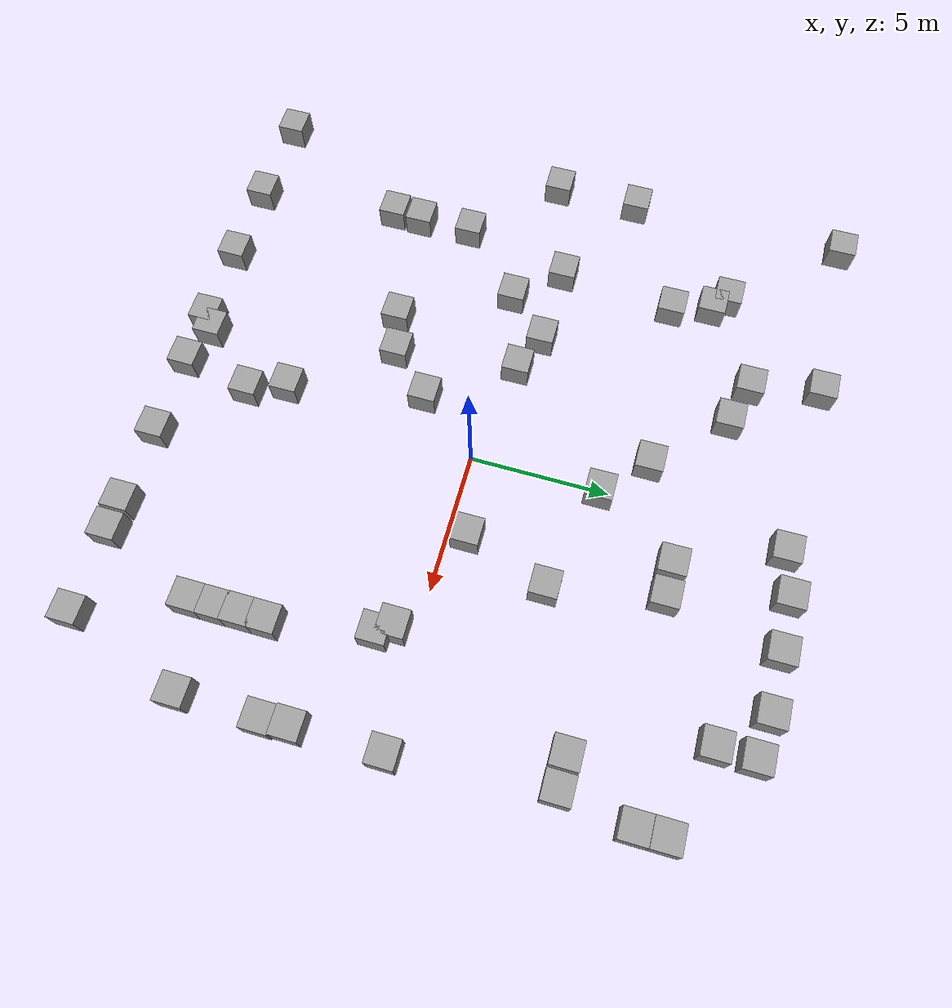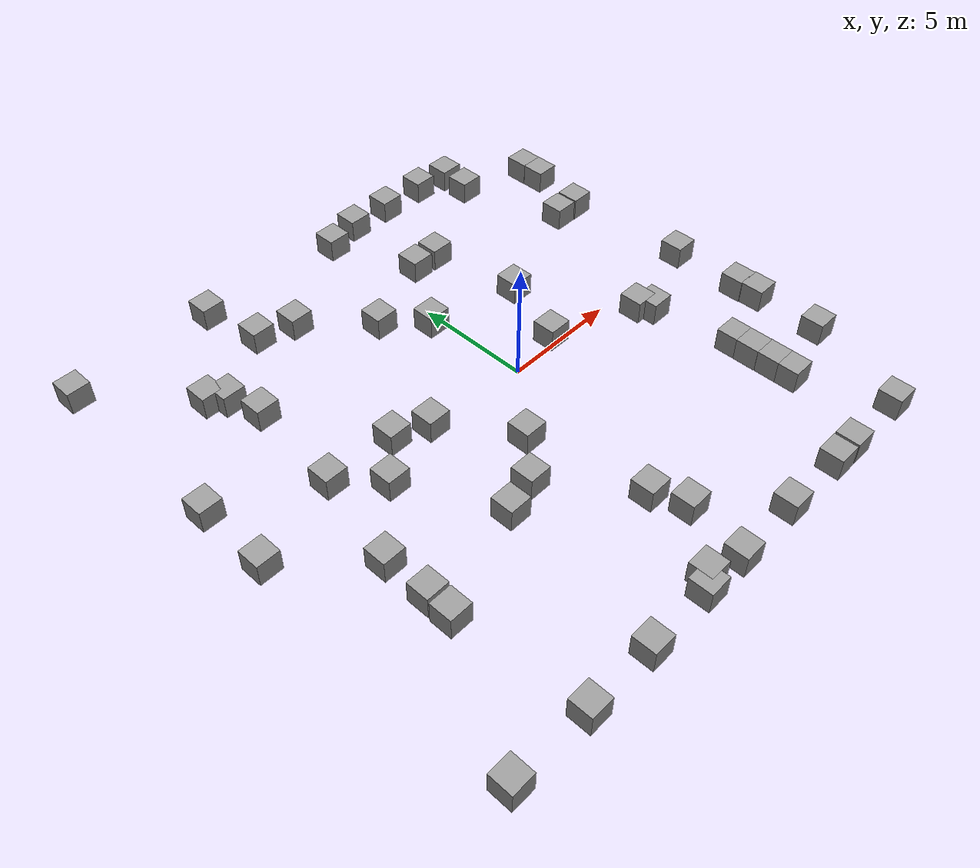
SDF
<?xml version='1.0'?>
<sdf version='1.7'>
  <model name='21'>
    <link name='link_0'>
      <inertial>
        <mass>1</mass>
        <inertia>
          <ixx>0.166667</ixx>
          <ixy>0</ixy>
          <ixz>0</ixz>
          <iyy>0.166667</iyy>
          <iyz>0</iyz>
          <izz>0.166667</izz>
        </inertia>
      </inertial>
      <pose>7.34424 10.0959 0 0 -0 0</pose>
      <visual name='visual'>
        <pose>0 0 0 0 -0 0</pose>
        <geometry>
          <box>
            <size>1 1 1</size>
          </box>
        </geometry>
        <material>
          <lighting>1</lighting>
          <script>
            <uri>file://media/materials/scripts/gazebo.material</uri>
            <name>Gazebo/Grey</name>
          </script>
          <shader type='pixel'/>
        </material>
        <transparency>0</transparency>
        <cast_shadows>1</cast_shadows>
      </visual>
      <collision name='collision'>
        <laser_retro>0</laser_retro>
        <max_contacts>10</max_contacts>
        <pose>0 0 0 0 -0 0</pose>
        <geometry>
          <box>
            <size>1 1 1</size>
          </box>
        </geometry>
        <surface>
          <friction>
            <ode>
              <mu>1</mu>
              <mu2>1</mu2>
              <fdir1>0 0 0</fdir1>
              <slip1>0</slip1>
              <slip2>0</slip2>
            </ode>
            <torsional>
              <coefficient>1</coefficient>
              <patch_radius>0</patch_radius>
              <surface_radius>0</surface_radius>
              <use_patch_radius>1</use_patch_radius>
              <ode>
                <slip>0</slip>
              </ode>
            </torsional>
          </friction>
          <bounce>
            <restitution_coefficient>0</restitution_coefficient>
            <threshold>1e+06</threshold>
          </bounce>
          <contact>
            <collide_without_contact>0</collide_without_contact>
            <collide_without_contact_bitmask>1</collide_without_contact_bitmask>
            <collide_bitmask>1</collide_bitmask>
            <ode>
              <soft_cfm>0</soft_cfm>
              <soft_erp>0.2</soft_erp>
              <kp>1e+13</kp>
              <kd>1</kd>
              <max_vel>0.01</max_vel>
              <min_depth>0</min_depth>
            </ode>
            <bullet>
              <split_impulse>1</split_impulse>
              <split_impulse_penetration_threshold>-0.01</split_impulse_penetration_threshold>
              <soft_cfm>0</soft_cfm>
              <soft_erp>0.2</soft_erp>
              <kp>1e+13</kp>
              <kd>1</kd>
            </bullet>
          </contact>
        </surface>
      </collision>
    </link>
    <link name='link_1'>
      <inertial>
        <mass>1</mass>
        <inertia>
          <ixx>0.166667</ixx>
          <ixy>0</ixy>
          <ixz>0</ixz>
          <iyy>0.166667</iyy>
          <iyz>0</iyz>
          <izz>0.166667</izz>
        </inertia>
      </inertial>
      <pose>10.3682 9.14937 0 0 -0 0</pose>
      <visual name='visual'>
        <pose>0 0 0 0 -0 0</pose>
        <geometry>
          <box>
            <size>1 1 1</size>
          </box>
        </geometry>
        <material>
          <lighting>1</lighting>
          <script>
            <uri>file://media/materials/scripts/gazebo.material</uri>
            <name>Gazebo/Grey</name>
          </script>
          <shader type='pixel'/>
        </material>
        <transparency>0</transparency>
        <cast_shadows>1</cast_shadows>
      </visual>
      <collision name='collision'>
        <laser_retro>0</laser_retro>
        <max_contacts>10</max_contacts>
        <pose>0 0 0 0 -0 0</pose>
        <geometry>
          <box>
            <size>1 1 1</size>
          </box>
        </geometry>
        <surface>
          <friction>
            <ode>
              <mu>1</mu>
              <mu2>1</mu2>
              <fdir1>0 0 0</fdir1>
              <slip1>0</slip1>
              <slip2>0</slip2>
            </ode>
            <torsional>
              <coefficient>1</coefficient>
              <patch_radius>0</patch_radius>
              <surface_radius>0</surface_radius>
              <use_patch_radius>1</use_patch_radius>
              <ode>
                <slip>0</slip>
              </ode>
            </torsional>
          </friction>
          <bounce>
            <restitution_coefficient>0</restitution_coefficient>
            <threshold>1e+06</threshold>
          </bounce>
          <contact>
            <collide_without_contact>0</collide_without_contact>
            <collide_without_contact_bitmask>1</collide_without_contact_bitmask>
            <collide_bitmask>1</collide_bitmask>
            <ode>
              <soft_cfm>0</soft_cfm>
              <soft_erp>0.2</soft_erp>
              <kp>1e+13</kp>
              <kd>1</kd>
              <max_vel>0.01</max_vel>
              <min_depth>0</min_depth>
            </ode>
            <bullet>
              <split_impulse>1</split_impulse>
              <split_impulse_penetration_threshold>-0.01</split_impulse_penetration_threshold>
              <soft_cfm>0</soft_cfm>
              <soft_erp>0.2</soft_erp>
              <kp>1e+13</kp>
              <kd>1</kd>
            </bullet>
          </contact>
        </surface>
      </collision>
    </link>
    <link name='link_10'>
      <inertial>
        <mass>1</mass>
        <inertia>
          <ixx>0.166667</ixx>
          <ixy>0</ixy>
          <ixz>0</ixz>
          <iyy>0.166667</iyy>
          <iyz>0</iyz>
          <izz>0.166667</izz>
        </inertia>
      </inertial>
      <pose>-6.1425 11.6478 0 0 -0 0</pose>
      <visual name='visual'>
        <pose>0 0 0 0 -0 0</pose>
        <geometry>
          <box>
            <size>1 1 1</size>
          </box>
        </geometry>
        <material>
          <lighting>1</lighting>
          <script>
            <uri>file://media/materials/scripts/gazebo.material</uri>
            <name>Gazebo/Grey</name>
          </script>
          <shader type='pixel'/>
        </material>
        <transparency>0</transparency>
        <cast_shadows>1</cast_shadows>
      </visual>
      <collision name='collision'>
        <laser_retro>0</laser_retro>
        <max_contacts>10</max_contacts>
        <pose>0 0 0 0 -0 0</pose>
        <geometry>
          <box>
            <size>1 1 1</size>
          </box>
        </geometry>
        <surface>
          <friction>
            <ode>
              <mu>1</mu>
              <mu2>1</mu2>
              <fdir1>0 0 0</fdir1>
              <slip1>0</slip1>
              <slip2>0</slip2>
            </ode>
            <torsional>
              <coefficient>1</coefficient>
              <patch_radius>0</patch_radius>
              <surface_radius>0</surface_radius>
              <use_patch_radius>1</use_patch_radius>
              <ode>
                <slip>0</slip>
              </ode>
            </torsional>
          </friction>
          <bounce>
            <restitution_coefficient>0</restitution_coefficient>
            <threshold>1e+06</threshold>
          </bounce>
          <contact>
            <collide_without_contact>0</collide_without_contact>
            <collide_without_contact_bitmask>1</collide_without_contact_bitmask>
            <collide_bitmask>1</collide_bitmask>
            <ode>
              <soft_cfm>0</soft_cfm>
              <soft_erp>0.2</soft_erp>
              <kp>1e+13</kp>
              <kd>1</kd>
              <max_vel>0.01</max_vel>
              <min_depth>0</min_depth>
            </ode>
            <bullet>
              <split_impulse>1</split_impulse>
              <split_impulse_penetration_threshold>-0.01</split_impulse_penetration_threshold>
              <soft_cfm>0</soft_cfm>
              <soft_erp>0.2</soft_erp>
              <kp>1e+13</kp>
              <kd>1</kd>
            </bullet>
          </contact>
        </surface>
      </collision>
    </link>
    <link name='link_11'>
      <inertial>
        <mass>1</mass>
        <inertia>
          <ixx>0.166667</ixx>
          <ixy>0</ixy>
          <ixz>0</ixz>
          <iyy>0.166667</iyy>
          <iyz>0</iyz>
          <izz>0.166667</izz>
        </inertia>
      </inertial>
      <pose>-0.123891 4.67345 0 0 -0 0</pose>
      <visual name='visual'>
        <pose>0 0 0 0 -0 0</pose>
        <geometry>
          <box>
            <size>1 1 1</size>
          </box>
        </geometry>
        <material>
          <lighting>1</lighting>
          <script>
            <uri>file://media/materials/scripts/gazebo.material</uri>
            <name>Gazebo/Grey</name>
          </script>
          <shader type='pixel'/>
        </material>
        <transparency>0</transparency>
        <cast_shadows>1</cast_shadows>
      </visual>
      <collision name='collision'>
        <laser_retro>0</laser_retro>
        <max_contacts>10</max_contacts>
        <pose>0 0 0 0 -0 0</pose>
        <geometry>
          <box>
            <size>1 1 1</size>
          </box>
        </geometry>
        <surface>
          <friction>
            <ode>
              <mu>1</mu>
              <mu2>1</mu2>
              <fdir1>0 0 0</fdir1>
              <slip1>0</slip1>
              <slip2>0</slip2>
            </ode>
            <torsional>
              <coefficient>1</coefficient>
              <patch_radius>0</patch_radius>
              <surface_radius>0</surface_radius>
              <use_patch_radius>1</use_patch_radius>
              <ode>
                <slip>0</slip>
              </ode>
            </torsional>
          </friction>
          <bounce>
            <restitution_coefficient>0</restitution_coefficient>
            <threshold>1e+06</threshold>
          </bounce>
          <contact>
            <collide_without_contact>0</collide_without_contact>
            <collide_without_contact_bitmask>1</collide_without_contact_bitmask>
            <collide_bitmask>1</collide_bitmask>
            <ode>
              <soft_cfm>0</soft_cfm>
              <soft_erp>0.2</soft_erp>
              <kp>1e+13</kp>
              <kd>1</kd>
              <max_vel>0.01</max_vel>
              <min_depth>0</min_depth>
            </ode>
            <bullet>
              <split_impulse>1</split_impulse>
              <split_impulse_penetration_threshold>-0.01</split_impulse_penetration_threshold>
              <soft_cfm>0</soft_cfm>
              <soft_erp>0.2</soft_erp>
              <kp>1e+13</kp>
              <kd>1</kd>
            </bullet>
          </contact>
        </surface>
      </collision>
    </link>
    <link name='link_12'>
      <inertial>
        <mass>1</mass>
        <inertia>
          <ixx>0.166667</ixx>
          <ixy>0</ixy>
          <ixz>0</ixz>
          <iyy>0.166667</iyy>
          <iyz>0</iyz>
          <izz>0.166667</izz>
        </inertia>
      </inertial>
      <pose>-1.64634 6.14844 0 0 -0 0</pose>
      <visual name='visual'>
        <pose>0 0 0 0 -0 0</pose>
        <geometry>
          <box>
            <size>1 1 1</size>
          </box>
        </geometry>
        <material>
          <lighting>1</lighting>
          <script>
            <uri>file://media/materials/scripts/gazebo.material</uri>
            <name>Gazebo/Grey</name>
          </script>
          <shader type='pixel'/>
        </material>
        <transparency>0</transparency>
        <cast_shadows>1</cast_shadows>
      </visual>
      <collision name='collision'>
        <laser_retro>0</laser_retro>
        <max_contacts>10</max_contacts>
        <pose>0 0 0 0 -0 0</pose>
        <geometry>
          <box>
            <size>1 1 1</size>
          </box>
        </geometry>
        <surface>
          <friction>
            <ode>
              <mu>1</mu>
              <mu2>1</mu2>
              <fdir1>0 0 0</fdir1>
              <slip1>0</slip1>
              <slip2>0</slip2>
            </ode>
            <torsional>
              <coefficient>1</coefficient>
              <patch_radius>0</patch_radius>
              <surface_radius>0</surface_radius>
              <use_patch_radius>1</use_patch_radius>
              <ode>
                <slip>0</slip>
              </ode>
            </torsional>
          </friction>
          <bounce>
            <restitution_coefficient>0</restitution_coefficient>
            <threshold>1e+06</threshold>
          </bounce>
          <contact>
            <collide_without_contact>0</collide_without_contact>
            <collide_without_contact_bitmask>1</collide_without_contact_bitmask>
            <collide_bitmask>1</collide_bitmask>
            <ode>
              <soft_cfm>0</soft_cfm>
              <soft_erp>0.2</soft_erp>
              <kp>1e+13</kp>
              <kd>1</kd>
              <max_vel>0.01</max_vel>
              <min_depth>0</min_depth>
            </ode>
            <bullet>
              <split_impulse>1</split_impulse>
              <split_impulse_penetration_threshold>-0.01</split_impulse_penetration_threshold>
              <soft_cfm>0</soft_cfm>
              <soft_erp>0.2</soft_erp>
              <kp>1e+13</kp>
              <kd>1</kd>
            </bullet>
          </contact>
        </surface>
      </collision>
    </link>
    <link name='link_13'>
      <inertial>
        <mass>1</mass>
        <inertia>
          <ixx>0.166667</ixx>
          <ixy>0</ixy>
          <ixz>0</ixz>
          <iyy>0.166667</iyy>
          <iyz>0</iyz>
          <izz>0.166667</izz>
        </inertia>
      </inertial>
      <pose>-4.05578 8.58638 0 0 -0 0</pose>
      <visual name='visual'>
        <pose>0 0 0 0 -0 0</pose>
        <geometry>
          <box>
            <size>1 1 1</size>
          </box>
        </geometry>
        <material>
          <lighting>1</lighting>
          <script>
            <uri>file://media/materials/scripts/gazebo.material</uri>
            <name>Gazebo/Grey</name>
          </script>
          <shader type='pixel'/>
        </material>
        <transparency>0</transparency>
        <cast_shadows>1</cast_shadows>
      </visual>
      <collision name='collision'>
        <laser_retro>0</laser_retro>
        <max_contacts>10</max_contacts>
        <pose>0 0 0 0 -0 0</pose>
        <geometry>
          <box>
            <size>1 1 1</size>
          </box>
        </geometry>
        <surface>
          <friction>
            <ode>
              <mu>1</mu>
              <mu2>1</mu2>
              <fdir1>0 0 0</fdir1>
              <slip1>0</slip1>
              <slip2>0</slip2>
            </ode>
            <torsional>
              <coefficient>1</coefficient>
              <patch_radius>0</patch_radius>
              <surface_radius>0</surface_radius>
              <use_patch_radius>1</use_patch_radius>
              <ode>
                <slip>0</slip>
              </ode>
            </torsional>
          </friction>
          <bounce>
            <restitution_coefficient>0</restitution_coefficient>
            <threshold>1e+06</threshold>
          </bounce>
          <contact>
            <collide_without_contact>0</collide_without_contact>
            <collide_without_contact_bitmask>1</collide_without_contact_bitmask>
            <collide_bitmask>1</collide_bitmask>
            <ode>
              <soft_cfm>0</soft_cfm>
              <soft_erp>0.2</soft_erp>
              <kp>1e+13</kp>
              <kd>1</kd>
              <max_vel>0.01</max_vel>
              <min_depth>0</min_depth>
            </ode>
            <bullet>
              <split_impulse>1</split_impulse>
              <split_impulse_penetration_threshold>-0.01</split_impulse_penetration_threshold>
              <soft_cfm>0</soft_cfm>
              <soft_erp>0.2</soft_erp>
              <kp>1e+13</kp>
              <kd>1</kd>
            </bullet>
          </contact>
        </surface>
      </collision>
    </link>
    <link name='link_14'>
      <inertial>
        <mass>1</mass>
        <inertia>
          <ixx>0.166667</ixx>
          <ixy>0</ixy>
          <ixz>0</ixz>
          <iyy>0.166667</iyy>
          <iyz>0</iyz>
          <izz>0.166667</izz>
        </inertia>
      </inertial>
      <pose>-5.62589 9.06819 0 0 -0 0</pose>
      <visual name='visual'>
        <pose>0 0 0 0 -0 0</pose>
        <geometry>
          <box>
            <size>1 1 1</size>
          </box>
        </geometry>
        <material>
          <lighting>1</lighting>
          <script>
            <uri>file://media/materials/scripts/gazebo.material</uri>
            <name>Gazebo/Grey</name>
          </script>
          <shader type='pixel'/>
        </material>
        <transparency>0</transparency>
        <cast_shadows>1</cast_shadows>
      </visual>
      <collision name='collision'>
        <laser_retro>0</laser_retro>
        <max_contacts>10</max_contacts>
        <pose>0 0 0 0 -0 0</pose>
        <geometry>
          <box>
            <size>1 1 1</size>
          </box>
        </geometry>
        <surface>
          <friction>
            <ode>
              <mu>1</mu>
              <mu2>1</mu2>
              <fdir1>0 0 0</fdir1>
              <slip1>0</slip1>
              <slip2>0</slip2>
            </ode>
            <torsional>
              <coefficient>1</coefficient>
              <patch_radius>0</patch_radius>
              <surface_radius>0</surface_radius>
              <use_patch_radius>1</use_patch_radius>
              <ode>
                <slip>0</slip>
              </ode>
            </torsional>
          </friction>
          <bounce>
            <restitution_coefficient>0</restitution_coefficient>
            <threshold>1e+06</threshold>
          </bounce>
          <contact>
            <collide_without_contact>0</collide_without_contact>
            <collide_without_contact_bitmask>1</collide_without_contact_bitmask>
            <collide_bitmask>1</collide_bitmask>
            <ode>
              <soft_cfm>0</soft_cfm>
              <soft_erp>0.2</soft_erp>
              <kp>1e+13</kp>
              <kd>1</kd>
              <max_vel>0.01</max_vel>
              <min_depth>0</min_depth>
            </ode>
            <bullet>
              <split_impulse>1</split_impulse>
              <split_impulse_penetration_threshold>-0.01</split_impulse_penetration_threshold>
              <soft_cfm>0</soft_cfm>
              <soft_erp>0.2</soft_erp>
              <kp>1e+13</kp>
              <kd>1</kd>
            </bullet>
          </contact>
        </surface>
      </collision>
    </link>
    <link name='link_15'>
      <inertial>
        <mass>1</mass>
        <inertia>
          <ixx>0.166667</ixx>
          <ixy>0</ixy>
          <ixz>0</ixz>
          <iyy>0.166667</iyy>
          <iyz>0</iyz>
          <izz>0.166667</izz>
        </inertia>
      </inertial>
      <pose>-12.5405 11.5403 0 0 -0 0</pose>
      <visual name='visual'>
        <pose>0 0 0 0 -0 0</pose>
        <geometry>
          <box>
            <size>1 1 1</size>
          </box>
        </geometry>
        <material>
          <lighting>1</lighting>
          <script>
            <uri>file://media/materials/scripts/gazebo.material</uri>
            <name>Gazebo/Grey</name>
          </script>
          <shader type='pixel'/>
        </material>
        <transparency>0</transparency>
        <cast_shadows>1</cast_shadows>
      </visual>
      <collision name='collision'>
        <laser_retro>0</laser_retro>
        <max_contacts>10</max_contacts>
        <pose>0 0 0 0 -0 0</pose>
        <geometry>
          <box>
            <size>1 1 1</size>
          </box>
        </geometry>
        <surface>
          <friction>
            <ode>
              <mu>1</mu>
              <mu2>1</mu2>
              <fdir1>0 0 0</fdir1>
              <slip1>0</slip1>
              <slip2>0</slip2>
            </ode>
            <torsional>
              <coefficient>1</coefficient>
              <patch_radius>0</patch_radius>
              <surface_radius>0</surface_radius>
              <use_patch_radius>1</use_patch_radius>
              <ode>
                <slip>0</slip>
              </ode>
            </torsional>
          </friction>
          <bounce>
            <restitution_coefficient>0</restitution_coefficient>
            <threshold>1e+06</threshold>
          </bounce>
          <contact>
            <collide_without_contact>0</collide_without_contact>
            <collide_without_contact_bitmask>1</collide_without_contact_bitmask>
            <collide_bitmask>1</collide_bitmask>
            <ode>
              <soft_cfm>0</soft_cfm>
              <soft_erp>0.2</soft_erp>
              <kp>1e+13</kp>
              <kd>1</kd>
              <max_vel>0.01</max_vel>
              <min_depth>0</min_depth>
            </ode>
            <bullet>
              <split_impulse>1</split_impulse>
              <split_impulse_penetration_threshold>-0.01</split_impulse_penetration_threshold>
              <soft_cfm>0</soft_cfm>
              <soft_erp>0.2</soft_erp>
              <kp>1e+13</kp>
              <kd>1</kd>
            </bullet>
          </contact>
        </surface>
      </collision>
    </link>
    <link name='link_16'>
      <inertial>
        <mass>1</mass>
        <inertia>
          <ixx>0.166667</ixx>
          <ixy>0</ixy>
          <ixz>0</ixz>
          <iyy>0.166667</iyy>
          <iyz>0</iyz>
          <izz>0.166667</izz>
        </inertia>
      </inertial>
      <pose>-12.5473 3.34768 0 0 -0 0</pose>
      <visual name='visual'>
        <pose>0 0 0 0 -0 0</pose>
        <geometry>
          <box>
            <size>1 1 1</size>
          </box>
        </geometry>
        <material>
          <lighting>1</lighting>
          <script>
            <uri>file://media/materials/scripts/gazebo.material</uri>
            <name>Gazebo/Grey</name>
          </script>
          <shader type='pixel'/>
        </material>
        <transparency>0</transparency>
        <cast_shadows>1</cast_shadows>
      </visual>
      <collision name='collision'>
        <laser_retro>0</laser_retro>
        <max_contacts>10</max_contacts>
        <pose>0 0 0 0 -0 0</pose>
        <geometry>
          <box>
            <size>1 1 1</size>
          </box>
        </geometry>
        <surface>
          <friction>
            <ode>
              <mu>1</mu>
              <mu2>1</mu2>
              <fdir1>0 0 0</fdir1>
              <slip1>0</slip1>
              <slip2>0</slip2>
            </ode>
            <torsional>
              <coefficient>1</coefficient>
              <patch_radius>0</patch_radius>
              <surface_radius>0</surface_radius>
              <use_patch_radius>1</use_patch_radius>
              <ode>
                <slip>0</slip>
              </ode>
            </torsional>
          </friction>
          <bounce>
            <restitution_coefficient>0</restitution_coefficient>
            <threshold>1e+06</threshold>
          </bounce>
          <contact>
            <collide_without_contact>0</collide_without_contact>
            <collide_without_contact_bitmask>1</collide_without_contact_bitmask>
            <collide_bitmask>1</collide_bitmask>
            <ode>
              <soft_cfm>0</soft_cfm>
              <soft_erp>0.2</soft_erp>
              <kp>1e+13</kp>
              <kd>1</kd>
              <max_vel>0.01</max_vel>
              <min_depth>0</min_depth>
            </ode>
            <bullet>
              <split_impulse>1</split_impulse>
              <split_impulse_penetration_threshold>-0.01</split_impulse_penetration_threshold>
              <soft_cfm>0</soft_cfm>
              <soft_erp>0.2</soft_erp>
              <kp>1e+13</kp>
              <kd>1</kd>
            </bullet>
          </contact>
        </surface>
      </collision>
    </link>
    <link name='link_17'>
      <inertial>
        <mass>1</mass>
        <inertia>
          <ixx>0.166667</ixx>
          <ixy>0</ixy>
          <ixz>0</ixz>
          <iyy>0.166667</iyy>
          <iyz>0</iyz>
          <izz>0.166667</izz>
        </inertia>
      </inertial>
      <pose>-12.5918 0.162825 0 0 -0 0</pose>
      <visual name='visual'>
        <pose>0 0 0 0 -0 0</pose>
        <geometry>
          <box>
            <size>1 1 1</size>
          </box>
        </geometry>
        <material>
          <lighting>1</lighting>
          <script>
            <uri>file://media/materials/scripts/gazebo.material</uri>
            <name>Gazebo/Grey</name>
          </script>
          <shader type='pixel'/>
        </material>
        <transparency>0</transparency>
        <cast_shadows>1</cast_shadows>
      </visual>
      <collision name='collision'>
        <laser_retro>0</laser_retro>
        <max_contacts>10</max_contacts>
        <pose>0 0 0 0 -0 0</pose>
        <geometry>
          <box>
            <size>1 1 1</size>
          </box>
        </geometry>
        <surface>
          <friction>
            <ode>
              <mu>1</mu>
              <mu2>1</mu2>
              <fdir1>0 0 0</fdir1>
              <slip1>0</slip1>
              <slip2>0</slip2>
            </ode>
            <torsional>
              <coefficient>1</coefficient>
              <patch_radius>0</patch_radius>
              <surface_radius>0</surface_radius>
              <use_patch_radius>1</use_patch_radius>
              <ode>
                <slip>0</slip>
              </ode>
            </torsional>
          </friction>
          <bounce>
            <restitution_coefficient>0</restitution_coefficient>
            <threshold>1e+06</threshold>
          </bounce>
          <contact>
            <collide_without_contact>0</collide_without_contact>
            <collide_without_contact_bitmask>1</collide_without_contact_bitmask>
            <collide_bitmask>1</collide_bitmask>
            <ode>
              <soft_cfm>0</soft_cfm>
              <soft_erp>0.2</soft_erp>
              <kp>1e+13</kp>
              <kd>1</kd>
              <max_vel>0.01</max_vel>
              <min_depth>0</min_depth>
            </ode>
            <bullet>
              <split_impulse>1</split_impulse>
              <split_impulse_penetration_threshold>-0.01</split_impulse_penetration_threshold>
              <soft_cfm>0</soft_cfm>
              <soft_erp>0.2</soft_erp>
              <kp>1e+13</kp>
              <kd>1</kd>
            </bullet>
          </contact>
        </surface>
      </collision>
    </link>
    <link name='link_18'>
      <inertial>
        <mass>1</mass>
        <inertia>
          <ixx>0.166667</ixx>
          <ixy>0</ixy>
          <ixz>0</ixz>
          <iyy>0.166667</iyy>
          <iyz>0</iyz>
          <izz>0.166667</izz>
        </inertia>
      </inertial>
      <pose>-8.61368 1.28544 0 0 -0 0</pose>
      <visual name='visual'>
        <pose>0 0 0 0 -0 0</pose>
        <geometry>
          <box>
            <size>1 1 1</size>
          </box>
        </geometry>
        <material>
          <lighting>1</lighting>
          <script>
            <uri>file://media/materials/scripts/gazebo.material</uri>
            <name>Gazebo/Grey</name>
          </script>
          <shader type='pixel'/>
        </material>
        <transparency>0</transparency>
        <cast_shadows>1</cast_shadows>
      </visual>
      <collision name='collision'>
        <laser_retro>0</laser_retro>
        <max_contacts>10</max_contacts>
        <pose>0 0 0 0 -0 0</pose>
        <geometry>
          <box>
            <size>1 1 1</size>
          </box>
        </geometry>
        <surface>
          <friction>
            <ode>
              <mu>1</mu>
              <mu2>1</mu2>
              <fdir1>0 0 0</fdir1>
              <slip1>0</slip1>
              <slip2>0</slip2>
            </ode>
            <torsional>
              <coefficient>1</coefficient>
              <patch_radius>0</patch_radius>
              <surface_radius>0</surface_radius>
              <use_patch_radius>1</use_patch_radius>
              <ode>
                <slip>0</slip>
              </ode>
            </torsional>
          </friction>
          <bounce>
            <restitution_coefficient>0</restitution_coefficient>
            <threshold>1e+06</threshold>
          </bounce>
          <contact>
            <collide_without_contact>0</collide_without_contact>
            <collide_without_contact_bitmask>1</collide_without_contact_bitmask>
            <collide_bitmask>1</collide_bitmask>
            <ode>
              <soft_cfm>0</soft_cfm>
              <soft_erp>0.2</soft_erp>
              <kp>1e+13</kp>
              <kd>1</kd>
              <max_vel>0.01</max_vel>
              <min_depth>0</min_depth>
            </ode>
            <bullet>
              <split_impulse>1</split_impulse>
              <split_impulse_penetration_threshold>-0.01</split_impulse_penetration_threshold>
              <soft_cfm>0</soft_cfm>
              <soft_erp>0.2</soft_erp>
              <kp>1e+13</kp>
              <kd>1</kd>
            </bullet>
          </contact>
        </surface>
      </collision>
    </link>
    <link name='link_19'>
      <inertial>
        <mass>1</mass>
        <inertia>
          <ixx>0.166667</ixx>
          <ixy>0</ixy>
          <ixz>0</ixz>
          <iyy>0.166667</iyy>
          <iyz>0</iyz>
          <izz>0.166667</izz>
        </inertia>
      </inertial>
      <pose>-9.62189 -2.76465 0 0 -0 0</pose>
      <visual name='visual'>
        <pose>0 0 0 0 -0 0</pose>
        <geometry>
          <box>
            <size>1 1 1</size>
          </box>
        </geometry>
        <material>
          <lighting>1</lighting>
          <script>
            <uri>file://media/materials/scripts/gazebo.material</uri>
            <name>Gazebo/Grey</name>
          </script>
          <shader type='pixel'/>
        </material>
        <transparency>0</transparency>
        <cast_shadows>1</cast_shadows>
      </visual>
      <collision name='collision'>
        <laser_retro>0</laser_retro>
        <max_contacts>10</max_contacts>
        <pose>0 0 0 0 -0 0</pose>
        <geometry>
          <box>
            <size>1 1 1</size>
          </box>
        </geometry>
        <surface>
          <friction>
            <ode>
              <mu>1</mu>
              <mu2>1</mu2>
              <fdir1>0 0 0</fdir1>
              <slip1>0</slip1>
              <slip2>0</slip2>
            </ode>
            <torsional>
              <coefficient>1</coefficient>
              <patch_radius>0</patch_radius>
              <surface_radius>0</surface_radius>
              <use_patch_radius>1</use_patch_radius>
              <ode>
                <slip>0</slip>
              </ode>
            </torsional>
          </friction>
          <bounce>
            <restitution_coefficient>0</restitution_coefficient>
            <threshold>1e+06</threshold>
          </bounce>
          <contact>
            <collide_without_contact>0</collide_without_contact>
            <collide_without_contact_bitmask>1</collide_without_contact_bitmask>
            <collide_bitmask>1</collide_bitmask>
            <ode>
              <soft_cfm>0</soft_cfm>
              <soft_erp>0.2</soft_erp>
              <kp>1e+13</kp>
              <kd>1</kd>
              <max_vel>0.01</max_vel>
              <min_depth>0</min_depth>
            </ode>
            <bullet>
              <split_impulse>1</split_impulse>
              <split_impulse_penetration_threshold>-0.01</split_impulse_penetration_threshold>
              <soft_cfm>0</soft_cfm>
              <soft_erp>0.2</soft_erp>
              <kp>1e+13</kp>
              <kd>1</kd>
            </bullet>
          </contact>
        </surface>
      </collision>
    </link>
    <link name='link_2'>
      <inertial>
        <mass>1</mass>
        <inertia>
          <ixx>0.166667</ixx>
          <ixy>0</ixy>
          <ixz>0</ixz>
          <iyy>0.166667</iyy>
          <iyz>0</iyz>
          <izz>0.166667</izz>
        </inertia>
      </inertial>
      <pose>10.3714 8.14523 0 0 -0 0</pose>
      <visual name='visual'>
        <pose>0 0 0 0 -0 0</pose>
        <geometry>
          <box>
            <size>1 1 1</size>
          </box>
        </geometry>
        <material>
          <lighting>1</lighting>
          <script>
            <uri>file://media/materials/scripts/gazebo.material</uri>
            <name>Gazebo/Grey</name>
          </script>
          <shader type='pixel'/>
        </material>
        <transparency>0</transparency>
        <cast_shadows>1</cast_shadows>
      </visual>
      <collision name='collision'>
        <laser_retro>0</laser_retro>
        <max_contacts>10</max_contacts>
        <pose>0 0 0 0 -0 0</pose>
        <geometry>
          <box>
            <size>1 1 1</size>
          </box>
        </geometry>
        <surface>
          <friction>
            <ode>
              <mu>1</mu>
              <mu2>1</mu2>
              <fdir1>0 0 0</fdir1>
              <slip1>0</slip1>
              <slip2>0</slip2>
            </ode>
            <torsional>
              <coefficient>1</coefficient>
              <patch_radius>0</patch_radius>
              <surface_radius>0</surface_radius>
              <use_patch_radius>1</use_patch_radius>
              <ode>
                <slip>0</slip>
              </ode>
            </torsional>
          </friction>
          <bounce>
            <restitution_coefficient>0</restitution_coefficient>
            <threshold>1e+06</threshold>
          </bounce>
          <contact>
            <collide_without_contact>0</collide_without_contact>
            <collide_without_contact_bitmask>1</collide_without_contact_bitmask>
            <collide_bitmask>1</collide_bitmask>
            <ode>
              <soft_cfm>0</soft_cfm>
              <soft_erp>0.2</soft_erp>
              <kp>1e+13</kp>
              <kd>1</kd>
              <max_vel>0.01</max_vel>
              <min_depth>0</min_depth>
            </ode>
            <bullet>
              <split_impulse>1</split_impulse>
              <split_impulse_penetration_threshold>-0.01</split_impulse_penetration_threshold>
              <soft_cfm>0</soft_cfm>
              <soft_erp>0.2</soft_erp>
              <kp>1e+13</kp>
              <kd>1</kd>
            </bullet>
          </contact>
        </surface>
      </collision>
    </link>
    <link name='link_20'>
      <inertial>
        <mass>1</mass>
        <inertia>
          <ixx>0.166667</ixx>
          <ixy>0</ixy>
          <ixz>0</ixz>
          <iyy>0.166667</iyy>
          <iyz>0</iyz>
          <izz>0.166667</izz>
        </inertia>
      </inertial>
      <pose>-9.6054 -4.79794 0 0 -0 0</pose>
      <visual name='visual'>
        <pose>0 0 0 0 -0 0</pose>
        <geometry>
          <box>
            <size>1 1 1</size>
          </box>
        </geometry>
        <material>
          <lighting>1</lighting>
          <script>
            <uri>file://media/materials/scripts/gazebo.material</uri>
            <name>Gazebo/Grey</name>
          </script>
          <shader type='pixel'/>
        </material>
        <transparency>0</transparency>
        <cast_shadows>1</cast_shadows>
      </visual>
      <collision name='collision'>
        <laser_retro>0</laser_retro>
        <max_contacts>10</max_contacts>
        <pose>0 0 0 0 -0 0</pose>
        <geometry>
          <box>
            <size>1 1 1</size>
          </box>
        </geometry>
        <surface>
          <friction>
            <ode>
              <mu>1</mu>
              <mu2>1</mu2>
              <fdir1>0 0 0</fdir1>
              <slip1>0</slip1>
              <slip2>0</slip2>
            </ode>
            <torsional>
              <coefficient>1</coefficient>
              <patch_radius>0</patch_radius>
              <surface_radius>0</surface_radius>
              <use_patch_radius>1</use_patch_radius>
              <ode>
                <slip>0</slip>
              </ode>
            </torsional>
          </friction>
          <bounce>
            <restitution_coefficient>0</restitution_coefficient>
            <threshold>1e+06</threshold>
          </bounce>
          <contact>
            <collide_without_contact>0</collide_without_contact>
            <collide_without_contact_bitmask>1</collide_without_contact_bitmask>
            <collide_bitmask>1</collide_bitmask>
            <ode>
              <soft_cfm>0</soft_cfm>
              <soft_erp>0.2</soft_erp>
              <kp>1e+13</kp>
              <kd>1</kd>
              <max_vel>0.01</max_vel>
              <min_depth>0</min_depth>
            </ode>
            <bullet>
              <split_impulse>1</split_impulse>
              <split_impulse_penetration_threshold>-0.01</split_impulse_penetration_threshold>
              <soft_cfm>0</soft_cfm>
              <soft_erp>0.2</soft_erp>
              <kp>1e+13</kp>
              <kd>1</kd>
            </bullet>
          </contact>
        </surface>
      </collision>
    </link>
    <link name='link_21'>
      <inertial>
        <mass>1</mass>
        <inertia>
          <ixx>0.166667</ixx>
          <ixy>0</ixy>
          <ixz>0</ixz>
          <iyy>0.166667</iyy>
          <iyz>0</iyz>
          <izz>0.166667</izz>
        </inertia>
      </inertial>
      <pose>-9.65502 -5.90562 0 0 -0 0</pose>
      <visual name='visual'>
        <pose>0 0 0 0 -0 0</pose>
        <geometry>
          <box>
            <size>1 1 1</size>
          </box>
        </geometry>
        <material>
          <lighting>1</lighting>
          <script>
            <uri>file://media/materials/scripts/gazebo.material</uri>
            <name>Gazebo/Grey</name>
          </script>
          <shader type='pixel'/>
        </material>
        <transparency>0</transparency>
        <cast_shadows>1</cast_shadows>
      </visual>
      <collision name='collision'>
        <laser_retro>0</laser_retro>
        <max_contacts>10</max_contacts>
        <pose>0 0 0 0 -0 0</pose>
        <geometry>
          <box>
            <size>1 1 1</size>
          </box>
        </geometry>
        <surface>
          <friction>
            <ode>
              <mu>1</mu>
              <mu2>1</mu2>
              <fdir1>0 0 0</fdir1>
              <slip1>0</slip1>
              <slip2>0</slip2>
            </ode>
            <torsional>
              <coefficient>1</coefficient>
              <patch_radius>0</patch_radius>
              <surface_radius>0</surface_radius>
              <use_patch_radius>1</use_patch_radius>
              <ode>
                <slip>0</slip>
              </ode>
            </torsional>
          </friction>
          <bounce>
            <restitution_coefficient>0</restitution_coefficient>
            <threshold>1e+06</threshold>
          </bounce>
          <contact>
            <collide_without_contact>0</collide_without_contact>
            <collide_without_contact_bitmask>1</collide_without_contact_bitmask>
            <collide_bitmask>1</collide_bitmask>
            <ode>
              <soft_cfm>0</soft_cfm>
              <soft_erp>0.2</soft_erp>
              <kp>1e+13</kp>
              <kd>1</kd>
              <max_vel>0.01</max_vel>
              <min_depth>0</min_depth>
            </ode>
            <bullet>
              <split_impulse>1</split_impulse>
              <split_impulse_penetration_threshold>-0.01</split_impulse_penetration_threshold>
              <soft_cfm>0</soft_cfm>
              <soft_erp>0.2</soft_erp>
              <kp>1e+13</kp>
              <kd>1</kd>
            </bullet>
          </contact>
        </surface>
      </collision>
    </link>
    <link name='link_22'>
      <inertial>
        <mass>1</mass>
        <inertia>
          <ixx>0.166667</ixx>
          <ixy>0</ixy>
          <ixz>0</ixz>
          <iyy>0.166667</iyy>
          <iyz>0</iyz>
          <izz>0.166667</izz>
        </inertia>
      </inertial>
      <pose>-12.5644 -11.2451 0 0 -0 0</pose>
      <visual name='visual'>
        <pose>0 0 0 0 -0 0</pose>
        <geometry>
          <box>
            <size>1 1 1</size>
          </box>
        </geometry>
        <material>
          <lighting>1</lighting>
          <script>
            <uri>file://media/materials/scripts/gazebo.material</uri>
            <name>Gazebo/Grey</name>
          </script>
          <shader type='pixel'/>
        </material>
        <transparency>0</transparency>
        <cast_shadows>1</cast_shadows>
      </visual>
      <collision name='collision'>
        <laser_retro>0</laser_retro>
        <max_contacts>10</max_contacts>
        <pose>0 0 0 0 -0 0</pose>
        <geometry>
          <box>
            <size>1 1 1</size>
          </box>
        </geometry>
        <surface>
          <friction>
            <ode>
              <mu>1</mu>
              <mu2>1</mu2>
              <fdir1>0 0 0</fdir1>
              <slip1>0</slip1>
              <slip2>0</slip2>
            </ode>
            <torsional>
              <coefficient>1</coefficient>
              <patch_radius>0</patch_radius>
              <surface_radius>0</surface_radius>
              <use_patch_radius>1</use_patch_radius>
              <ode>
                <slip>0</slip>
              </ode>
            </torsional>
          </friction>
          <bounce>
            <restitution_coefficient>0</restitution_coefficient>
            <threshold>1e+06</threshold>
          </bounce>
          <contact>
            <collide_without_contact>0</collide_without_contact>
            <collide_without_contact_bitmask>1</collide_without_contact_bitmask>
            <collide_bitmask>1</collide_bitmask>
            <ode>
              <soft_cfm>0</soft_cfm>
              <soft_erp>0.2</soft_erp>
              <kp>1e+13</kp>
              <kd>1</kd>
              <max_vel>0.01</max_vel>
              <min_depth>0</min_depth>
            </ode>
            <bullet>
              <split_impulse>1</split_impulse>
              <split_impulse_penetration_threshold>-0.01</split_impulse_penetration_threshold>
              <soft_cfm>0</soft_cfm>
              <soft_erp>0.2</soft_erp>
              <kp>1e+13</kp>
              <kd>1</kd>
            </bullet>
          </contact>
        </surface>
      </collision>
    </link>
    <link name='link_23'>
      <inertial>
        <mass>1</mass>
        <inertia>
          <ixx>0.166667</ixx>
          <ixy>0</ixy>
          <ixz>0</ixz>
          <iyy>0.166667</iyy>
          <iyz>0</iyz>
          <izz>0.166667</izz>
        </inertia>
      </inertial>
      <pose>-5.11832 -4.3468 0 0 -0 0</pose>
      <visual name='visual'>
        <pose>0 0 0 0 -0 0</pose>
        <geometry>
          <box>
            <size>1 1 1</size>
          </box>
        </geometry>
        <material>
          <lighting>1</lighting>
          <script>
            <uri>file://media/materials/scripts/gazebo.material</uri>
            <name>Gazebo/Grey</name>
          </script>
          <shader type='pixel'/>
        </material>
        <transparency>0</transparency>
        <cast_shadows>1</cast_shadows>
      </visual>
      <collision name='collision'>
        <laser_retro>0</laser_retro>
        <max_contacts>10</max_contacts>
        <pose>0 0 0 0 -0 0</pose>
        <geometry>
          <box>
            <size>1 1 1</size>
          </box>
        </geometry>
        <surface>
          <friction>
            <ode>
              <mu>1</mu>
              <mu2>1</mu2>
              <fdir1>0 0 0</fdir1>
              <slip1>0</slip1>
              <slip2>0</slip2>
            </ode>
            <torsional>
              <coefficient>1</coefficient>
              <patch_radius>0</patch_radius>
              <surface_radius>0</surface_radius>
              <use_patch_radius>1</use_patch_radius>
              <ode>
                <slip>0</slip>
              </ode>
            </torsional>
          </friction>
          <bounce>
            <restitution_coefficient>0</restitution_coefficient>
            <threshold>1e+06</threshold>
          </bounce>
          <contact>
            <collide_without_contact>0</collide_without_contact>
            <collide_without_contact_bitmask>1</collide_without_contact_bitmask>
            <collide_bitmask>1</collide_bitmask>
            <ode>
              <soft_cfm>0</soft_cfm>
              <soft_erp>0.2</soft_erp>
              <kp>1e+13</kp>
              <kd>1</kd>
              <max_vel>0.01</max_vel>
              <min_depth>0</min_depth>
            </ode>
            <bullet>
              <split_impulse>1</split_impulse>
              <split_impulse_penetration_threshold>-0.01</split_impulse_penetration_threshold>
              <soft_cfm>0</soft_cfm>
              <soft_erp>0.2</soft_erp>
              <kp>1e+13</kp>
              <kd>1</kd>
            </bullet>
          </contact>
        </surface>
      </collision>
    </link>
    <link name='link_24'>
      <inertial>
        <mass>1</mass>
        <inertia>
          <ixx>0.166667</ixx>
          <ixy>0</ixy>
          <ixz>0</ixz>
          <iyy>0.166667</iyy>
          <iyz>0</iyz>
          <izz>0.166667</izz>
        </inertia>
      </inertial>
      <pose>-6.11914 -11.3527 0 0 -0 0</pose>
      <visual name='visual'>
        <pose>0 0 0 0 -0 0</pose>
        <geometry>
          <box>
            <size>1 1 1</size>
          </box>
        </geometry>
        <material>
          <lighting>1</lighting>
          <script>
            <uri>file://media/materials/scripts/gazebo.material</uri>
            <name>Gazebo/Grey</name>
          </script>
          <shader type='pixel'/>
        </material>
        <transparency>0</transparency>
        <cast_shadows>1</cast_shadows>
      </visual>
      <collision name='collision'>
        <laser_retro>0</laser_retro>
        <max_contacts>10</max_contacts>
        <pose>0 0 0 0 -0 0</pose>
        <geometry>
          <box>
            <size>1 1 1</size>
          </box>
        </geometry>
        <surface>
          <friction>
            <ode>
              <mu>1</mu>
              <mu2>1</mu2>
              <fdir1>0 0 0</fdir1>
              <slip1>0</slip1>
              <slip2>0</slip2>
            </ode>
            <torsional>
              <coefficient>1</coefficient>
              <patch_radius>0</patch_radius>
              <surface_radius>0</surface_radius>
              <use_patch_radius>1</use_patch_radius>
              <ode>
                <slip>0</slip>
              </ode>
            </torsional>
          </friction>
          <bounce>
            <restitution_coefficient>0</restitution_coefficient>
            <threshold>1e+06</threshold>
          </bounce>
          <contact>
            <collide_without_contact>0</collide_without_contact>
            <collide_without_contact_bitmask>1</collide_without_contact_bitmask>
            <collide_bitmask>1</collide_bitmask>
            <ode>
              <soft_cfm>0</soft_cfm>
              <soft_erp>0.2</soft_erp>
              <kp>1e+13</kp>
              <kd>1</kd>
              <max_vel>0.01</max_vel>
              <min_depth>0</min_depth>
            </ode>
            <bullet>
              <split_impulse>1</split_impulse>
              <split_impulse_penetration_threshold>-0.01</split_impulse_penetration_threshold>
              <soft_cfm>0</soft_cfm>
              <soft_erp>0.2</soft_erp>
              <kp>1e+13</kp>
              <kd>1</kd>
            </bullet>
          </contact>
        </surface>
      </collision>
    </link>
    <link name='link_25'>
      <inertial>
        <mass>1</mass>
        <inertia>
          <ixx>0.166667</ixx>
          <ixy>0</ixy>
          <ixz>0</ixz>
          <iyy>0.166667</iyy>
          <iyz>0</iyz>
          <izz>0.166667</izz>
        </inertia>
      </inertial>
      <pose>-9.16095 -11.3362 0 0 -0 0</pose>
      <visual name='visual'>
        <pose>0 0 0 0 -0 0</pose>
        <geometry>
          <box>
            <size>1 1 1</size>
          </box>
        </geometry>
        <material>
          <lighting>1</lighting>
          <script>
            <uri>file://media/materials/scripts/gazebo.material</uri>
            <name>Gazebo/Grey</name>
          </script>
          <shader type='pixel'/>
        </material>
        <transparency>0</transparency>
        <cast_shadows>1</cast_shadows>
      </visual>
      <collision name='collision'>
        <laser_retro>0</laser_retro>
        <max_contacts>10</max_contacts>
        <pose>0 0 0 0 -0 0</pose>
        <geometry>
          <box>
            <size>1 1 1</size>
          </box>
        </geometry>
        <surface>
          <friction>
            <ode>
              <mu>1</mu>
              <mu2>1</mu2>
              <fdir1>0 0 0</fdir1>
              <slip1>0</slip1>
              <slip2>0</slip2>
            </ode>
            <torsional>
              <coefficient>1</coefficient>
              <patch_radius>0</patch_radius>
              <surface_radius>0</surface_radius>
              <use_patch_radius>1</use_patch_radius>
              <ode>
                <slip>0</slip>
              </ode>
            </torsional>
          </friction>
          <bounce>
            <restitution_coefficient>0</restitution_coefficient>
            <threshold>1e+06</threshold>
          </bounce>
          <contact>
            <collide_without_contact>0</collide_without_contact>
            <collide_without_contact_bitmask>1</collide_without_contact_bitmask>
            <collide_bitmask>1</collide_bitmask>
            <ode>
              <soft_cfm>0</soft_cfm>
              <soft_erp>0.2</soft_erp>
              <kp>1e+13</kp>
              <kd>1</kd>
              <max_vel>0.01</max_vel>
              <min_depth>0</min_depth>
            </ode>
            <bullet>
              <split_impulse>1</split_impulse>
              <split_impulse_penetration_threshold>-0.01</split_impulse_penetration_threshold>
              <soft_cfm>0</soft_cfm>
              <soft_erp>0.2</soft_erp>
              <kp>1e+13</kp>
              <kd>1</kd>
            </bullet>
          </contact>
        </surface>
      </collision>
    </link>
    <link name='link_26'>
      <inertial>
        <mass>1</mass>
        <inertia>
          <ixx>0.166667</ixx>
          <ixy>0</ixy>
          <ixz>0</ixz>
          <iyy>0.166667</iyy>
          <iyz>0</iyz>
          <izz>0.166667</izz>
        </inertia>
      </inertial>
      <pose>-1.11812 -7.33722 0 0 -0 0</pose>
      <visual name='visual'>
        <pose>0 0 0 0 -0 0</pose>
        <geometry>
          <box>
            <size>1 1 1</size>
          </box>
        </geometry>
        <material>
          <lighting>1</lighting>
          <script>
            <uri>file://media/materials/scripts/gazebo.material</uri>
            <name>Gazebo/Grey</name>
          </script>
          <shader type='pixel'/>
        </material>
        <transparency>0</transparency>
        <cast_shadows>1</cast_shadows>
      </visual>
      <collision name='collision'>
        <laser_retro>0</laser_retro>
        <max_contacts>10</max_contacts>
        <pose>0 0 0 0 -0 0</pose>
        <geometry>
          <box>
            <size>1 1 1</size>
          </box>
        </geometry>
        <surface>
          <friction>
            <ode>
              <mu>1</mu>
              <mu2>1</mu2>
              <fdir1>0 0 0</fdir1>
              <slip1>0</slip1>
              <slip2>0</slip2>
            </ode>
            <torsional>
              <coefficient>1</coefficient>
              <patch_radius>0</patch_radius>
              <surface_radius>0</surface_radius>
              <use_patch_radius>1</use_patch_radius>
              <ode>
                <slip>0</slip>
              </ode>
            </torsional>
          </friction>
          <bounce>
            <restitution_coefficient>0</restitution_coefficient>
            <threshold>1e+06</threshold>
          </bounce>
          <contact>
            <collide_without_contact>0</collide_without_contact>
            <collide_without_contact_bitmask>1</collide_without_contact_bitmask>
            <collide_bitmask>1</collide_bitmask>
            <ode>
              <soft_cfm>0</soft_cfm>
              <soft_erp>0.2</soft_erp>
              <kp>1e+13</kp>
              <kd>1</kd>
              <max_vel>0.01</max_vel>
              <min_depth>0</min_depth>
            </ode>
            <bullet>
              <split_impulse>1</split_impulse>
              <split_impulse_penetration_threshold>-0.01</split_impulse_penetration_threshold>
              <soft_cfm>0</soft_cfm>
              <soft_erp>0.2</soft_erp>
              <kp>1e+13</kp>
              <kd>1</kd>
            </bullet>
          </contact>
        </surface>
      </collision>
    </link>
    <link name='link_27'>
      <inertial>
        <mass>1</mass>
        <inertia>
          <ixx>0.166667</ixx>
          <ixy>0</ixy>
          <ixz>0</ixz>
          <iyy>0.166667</iyy>
          <iyz>0</iyz>
          <izz>0.166667</izz>
        </inertia>
      </inertial>
      <pose>-0.622145 -8.72573 0 0 -0 0</pose>
      <visual name='visual'>
        <pose>0 0 0 0 -0 0</pose>
        <geometry>
          <box>
            <size>1 1 1</size>
          </box>
        </geometry>
        <material>
          <lighting>1</lighting>
          <script>
            <uri>file://media/materials/scripts/gazebo.material</uri>
            <name>Gazebo/Grey</name>
          </script>
          <shader type='pixel'/>
        </material>
        <transparency>0</transparency>
        <cast_shadows>1</cast_shadows>
      </visual>
      <collision name='collision'>
        <laser_retro>0</laser_retro>
        <max_contacts>10</max_contacts>
        <pose>0 0 0 0 -0 0</pose>
        <geometry>
          <box>
            <size>1 1 1</size>
          </box>
        </geometry>
        <surface>
          <friction>
            <ode>
              <mu>1</mu>
              <mu2>1</mu2>
              <fdir1>0 0 0</fdir1>
              <slip1>0</slip1>
              <slip2>0</slip2>
            </ode>
            <torsional>
              <coefficient>1</coefficient>
              <patch_radius>0</patch_radius>
              <surface_radius>0</surface_radius>
              <use_patch_radius>1</use_patch_radius>
              <ode>
                <slip>0</slip>
              </ode>
            </torsional>
          </friction>
          <bounce>
            <restitution_coefficient>0</restitution_coefficient>
            <threshold>1e+06</threshold>
          </bounce>
          <contact>
            <collide_without_contact>0</collide_without_contact>
            <collide_without_contact_bitmask>1</collide_without_contact_bitmask>
            <collide_bitmask>1</collide_bitmask>
            <ode>
              <soft_cfm>0</soft_cfm>
              <soft_erp>0.2</soft_erp>
              <kp>1e+13</kp>
              <kd>1</kd>
              <max_vel>0.01</max_vel>
              <min_depth>0</min_depth>
            </ode>
            <bullet>
              <split_impulse>1</split_impulse>
              <split_impulse_penetration_threshold>-0.01</split_impulse_penetration_threshold>
              <soft_cfm>0</soft_cfm>
              <soft_erp>0.2</soft_erp>
              <kp>1e+13</kp>
              <kd>1</kd>
            </bullet>
          </contact>
        </surface>
      </collision>
    </link>
    <link name='link_28'>
      <inertial>
        <mass>1</mass>
        <inertia>
          <ixx>0.166667</ixx>
          <ixy>0</ixy>
          <ixz>0</ixz>
          <iyy>0.166667</iyy>
          <iyz>0</iyz>
          <izz>0.166667</izz>
        </inertia>
      </inertial>
      <pose>-3.11836 -11.3212 0 0 -0 0</pose>
      <visual name='visual'>
        <pose>0 0 0 0 -0 0</pose>
        <geometry>
          <box>
            <size>1 1 1</size>
          </box>
        </geometry>
        <material>
          <lighting>1</lighting>
          <script>
            <uri>file://media/materials/scripts/gazebo.material</uri>
            <name>Gazebo/Grey</name>
          </script>
          <shader type='pixel'/>
        </material>
        <transparency>0</transparency>
        <cast_shadows>1</cast_shadows>
      </visual>
      <collision name='collision'>
        <laser_retro>0</laser_retro>
        <max_contacts>10</max_contacts>
        <pose>0 0 0 0 -0 0</pose>
        <geometry>
          <box>
            <size>1 1 1</size>
          </box>
        </geometry>
        <surface>
          <friction>
            <ode>
              <mu>1</mu>
              <mu2>1</mu2>
              <fdir1>0 0 0</fdir1>
              <slip1>0</slip1>
              <slip2>0</slip2>
            </ode>
            <torsional>
              <coefficient>1</coefficient>
              <patch_radius>0</patch_radius>
              <surface_radius>0</surface_radius>
              <use_patch_radius>1</use_patch_radius>
              <ode>
                <slip>0</slip>
              </ode>
            </torsional>
          </friction>
          <bounce>
            <restitution_coefficient>0</restitution_coefficient>
            <threshold>1e+06</threshold>
          </bounce>
          <contact>
            <collide_without_contact>0</collide_without_contact>
            <collide_without_contact_bitmask>1</collide_without_contact_bitmask>
            <collide_bitmask>1</collide_bitmask>
            <ode>
              <soft_cfm>0</soft_cfm>
              <soft_erp>0.2</soft_erp>
              <kp>1e+13</kp>
              <kd>1</kd>
              <max_vel>0.01</max_vel>
              <min_depth>0</min_depth>
            </ode>
            <bullet>
              <split_impulse>1</split_impulse>
              <split_impulse_penetration_threshold>-0.01</split_impulse_penetration_threshold>
              <soft_cfm>0</soft_cfm>
              <soft_erp>0.2</soft_erp>
              <kp>1e+13</kp>
              <kd>1</kd>
            </bullet>
          </contact>
        </surface>
      </collision>
    </link>
    <link name='link_29'>
      <inertial>
        <mass>1</mass>
        <inertia>
          <ixx>0.166667</ixx>
          <ixy>0</ixy>
          <ixz>0</ixz>
          <iyy>0.166667</iyy>
          <iyz>0</iyz>
          <izz>0.166667</izz>
        </inertia>
      </inertial>
      <pose>-2.6059 -10.9411 0 0 -0 0</pose>
      <visual name='visual'>
        <pose>0 0 0 0 -0 0</pose>
        <geometry>
          <box>
            <size>1 1 1</size>
          </box>
        </geometry>
        <material>
          <lighting>1</lighting>
          <script>
            <uri>file://media/materials/scripts/gazebo.material</uri>
            <name>Gazebo/Grey</name>
          </script>
          <shader type='pixel'/>
        </material>
        <transparency>0</transparency>
        <cast_shadows>1</cast_shadows>
      </visual>
      <collision name='collision'>
        <laser_retro>0</laser_retro>
        <max_contacts>10</max_contacts>
        <pose>0 0 0 0 -0 0</pose>
        <geometry>
          <box>
            <size>1 1 1</size>
          </box>
        </geometry>
        <surface>
          <friction>
            <ode>
              <mu>1</mu>
              <mu2>1</mu2>
              <fdir1>0 0 0</fdir1>
              <slip1>0</slip1>
              <slip2>0</slip2>
            </ode>
            <torsional>
              <coefficient>1</coefficient>
              <patch_radius>0</patch_radius>
              <surface_radius>0</surface_radius>
              <use_patch_radius>1</use_patch_radius>
              <ode>
                <slip>0</slip>
              </ode>
            </torsional>
          </friction>
          <bounce>
            <restitution_coefficient>0</restitution_coefficient>
            <threshold>1e+06</threshold>
          </bounce>
          <contact>
            <collide_without_contact>0</collide_without_contact>
            <collide_without_contact_bitmask>1</collide_without_contact_bitmask>
            <collide_bitmask>1</collide_bitmask>
            <ode>
              <soft_cfm>0</soft_cfm>
              <soft_erp>0.2</soft_erp>
              <kp>1e+13</kp>
              <kd>1</kd>
              <max_vel>0.01</max_vel>
              <min_depth>0</min_depth>
            </ode>
            <bullet>
              <split_impulse>1</split_impulse>
              <split_impulse_penetration_threshold>-0.01</split_impulse_penetration_threshold>
              <soft_cfm>0</soft_cfm>
              <soft_erp>0.2</soft_erp>
              <kp>1e+13</kp>
              <kd>1</kd>
            </bullet>
          </contact>
        </surface>
      </collision>
    </link>
    <link name='link_3'>
      <inertial>
        <mass>1</mass>
        <inertia>
          <ixx>0.166667</ixx>
          <ixy>0</ixy>
          <ixz>0</ixz>
          <iyy>0.166667</iyy>
          <iyz>0</iyz>
          <izz>0.166667</izz>
        </inertia>
      </inertial>
      <pose>9.92416 5.64013 0 0 -0 0</pose>
      <visual name='visual'>
        <pose>0 0 0 0 -0 0</pose>
        <geometry>
          <box>
            <size>1 1 1</size>
          </box>
        </geometry>
        <material>
          <lighting>1</lighting>
          <script>
            <uri>file://media/materials/scripts/gazebo.material</uri>
            <name>Gazebo/Grey</name>
          </script>
          <shader type='pixel'/>
        </material>
        <transparency>0</transparency>
        <cast_shadows>1</cast_shadows>
      </visual>
      <collision name='collision'>
        <laser_retro>0</laser_retro>
        <max_contacts>10</max_contacts>
        <pose>0 0 0 0 -0 0</pose>
        <geometry>
          <box>
            <size>1 1 1</size>
          </box>
        </geometry>
        <surface>
          <friction>
            <ode>
              <mu>1</mu>
              <mu2>1</mu2>
              <fdir1>0 0 0</fdir1>
              <slip1>0</slip1>
              <slip2>0</slip2>
            </ode>
            <torsional>
              <coefficient>1</coefficient>
              <patch_radius>0</patch_radius>
              <surface_radius>0</surface_radius>
              <use_patch_radius>1</use_patch_radius>
              <ode>
                <slip>0</slip>
              </ode>
            </torsional>
          </friction>
          <bounce>
            <restitution_coefficient>0</restitution_coefficient>
            <threshold>1e+06</threshold>
          </bounce>
          <contact>
            <collide_without_contact>0</collide_without_contact>
            <collide_without_contact_bitmask>1</collide_without_contact_bitmask>
            <collide_bitmask>1</collide_bitmask>
            <ode>
              <soft_cfm>0</soft_cfm>
              <soft_erp>0.2</soft_erp>
              <kp>1e+13</kp>
              <kd>1</kd>
              <max_vel>0.01</max_vel>
              <min_depth>0</min_depth>
            </ode>
            <bullet>
              <split_impulse>1</split_impulse>
              <split_impulse_penetration_threshold>-0.01</split_impulse_penetration_threshold>
              <soft_cfm>0</soft_cfm>
              <soft_erp>0.2</soft_erp>
              <kp>1e+13</kp>
              <kd>1</kd>
            </bullet>
          </contact>
        </surface>
      </collision>
    </link>
    <link name='link_30'>
      <inertial>
        <mass>1</mass>
        <inertia>
          <ixx>0.166667</ixx>
          <ixy>0</ixy>
          <ixz>0</ixz>
          <iyy>0.166667</iyy>
          <iyz>0</iyz>
          <izz>0.166667</izz>
        </inertia>
      </inertial>
      <pose>-1.15114 -11.3377 0 0 -0 0</pose>
      <visual name='visual'>
        <pose>0 0 0 0 -0 0</pose>
        <geometry>
          <box>
            <size>1 1 1</size>
          </box>
        </geometry>
        <material>
          <lighting>1</lighting>
          <script>
            <uri>file://media/materials/scripts/gazebo.material</uri>
            <name>Gazebo/Grey</name>
          </script>
          <shader type='pixel'/>
        </material>
        <transparency>0</transparency>
        <cast_shadows>1</cast_shadows>
      </visual>
      <collision name='collision'>
        <laser_retro>0</laser_retro>
        <max_contacts>10</max_contacts>
        <pose>0 0 0 0 -0 0</pose>
        <geometry>
          <box>
            <size>1 1 1</size>
          </box>
        </geometry>
        <surface>
          <friction>
            <ode>
              <mu>1</mu>
              <mu2>1</mu2>
              <fdir1>0 0 0</fdir1>
              <slip1>0</slip1>
              <slip2>0</slip2>
            </ode>
            <torsional>
              <coefficient>1</coefficient>
              <patch_radius>0</patch_radius>
              <surface_radius>0</surface_radius>
              <use_patch_radius>1</use_patch_radius>
              <ode>
                <slip>0</slip>
              </ode>
            </torsional>
          </friction>
          <bounce>
            <restitution_coefficient>0</restitution_coefficient>
            <threshold>1e+06</threshold>
          </bounce>
          <contact>
            <collide_without_contact>0</collide_without_contact>
            <collide_without_contact_bitmask>1</collide_without_contact_bitmask>
            <collide_bitmask>1</collide_bitmask>
            <ode>
              <soft_cfm>0</soft_cfm>
              <soft_erp>0.2</soft_erp>
              <kp>1e+13</kp>
              <kd>1</kd>
              <max_vel>0.01</max_vel>
              <min_depth>0</min_depth>
            </ode>
            <bullet>
              <split_impulse>1</split_impulse>
              <split_impulse_penetration_threshold>-0.01</split_impulse_penetration_threshold>
              <soft_cfm>0</soft_cfm>
              <soft_erp>0.2</soft_erp>
              <kp>1e+13</kp>
              <kd>1</kd>
            </bullet>
          </contact>
        </surface>
      </collision>
    </link>
    <link name='link_31'>
      <inertial>
        <mass>1</mass>
        <inertia>
          <ixx>0.166667</ixx>
          <ixy>0</ixy>
          <ixz>0</ixz>
          <iyy>0.166667</iyy>
          <iyz>0</iyz>
          <izz>0.166667</izz>
        </inertia>
      </inertial>
      <pose>1.83997 -11.3011 0 0 -0 0</pose>
      <visual name='visual'>
        <pose>0 0 0 0 -0 0</pose>
        <geometry>
          <box>
            <size>1 1 1</size>
          </box>
        </geometry>
        <material>
          <lighting>1</lighting>
          <script>
            <uri>file://media/materials/scripts/gazebo.material</uri>
            <name>Gazebo/Grey</name>
          </script>
          <shader type='pixel'/>
        </material>
        <transparency>0</transparency>
        <cast_shadows>1</cast_shadows>
      </visual>
      <collision name='collision'>
        <laser_retro>0</laser_retro>
        <max_contacts>10</max_contacts>
        <pose>0 0 0 0 -0 0</pose>
        <geometry>
          <box>
            <size>1 1 1</size>
          </box>
        </geometry>
        <surface>
          <friction>
            <ode>
              <mu>1</mu>
              <mu2>1</mu2>
              <fdir1>0 0 0</fdir1>
              <slip1>0</slip1>
              <slip2>0</slip2>
            </ode>
            <torsional>
              <coefficient>1</coefficient>
              <patch_radius>0</patch_radius>
              <surface_radius>0</surface_radius>
              <use_patch_radius>1</use_patch_radius>
              <ode>
                <slip>0</slip>
              </ode>
            </torsional>
          </friction>
          <bounce>
            <restitution_coefficient>0</restitution_coefficient>
            <threshold>1e+06</threshold>
          </bounce>
          <contact>
            <collide_without_contact>0</collide_without_contact>
            <collide_without_contact_bitmask>1</collide_without_contact_bitmask>
            <collide_bitmask>1</collide_bitmask>
            <ode>
              <soft_cfm>0</soft_cfm>
              <soft_erp>0.2</soft_erp>
              <kp>1e+13</kp>
              <kd>1</kd>
              <max_vel>0.01</max_vel>
              <min_depth>0</min_depth>
            </ode>
            <bullet>
              <split_impulse>1</split_impulse>
              <split_impulse_penetration_threshold>-0.01</split_impulse_penetration_threshold>
              <soft_cfm>0</soft_cfm>
              <soft_erp>0.2</soft_erp>
              <kp>1e+13</kp>
              <kd>1</kd>
            </bullet>
          </contact>
        </surface>
      </collision>
    </link>
    <link name='link_32'>
      <inertial>
        <mass>1</mass>
        <inertia>
          <ixx>0.166667</ixx>
          <ixy>0</ixy>
          <ixz>0</ixz>
          <iyy>0.166667</iyy>
          <iyz>0</iyz>
          <izz>0.166667</izz>
        </inertia>
      </inertial>
      <pose>5.82411 -11.3316 0 0 -0 0</pose>
      <visual name='visual'>
        <pose>0 0 0 0 -0 0</pose>
        <geometry>
          <box>
            <size>1 1 1</size>
          </box>
        </geometry>
        <material>
          <lighting>1</lighting>
          <script>
            <uri>file://media/materials/scripts/gazebo.material</uri>
            <name>Gazebo/Grey</name>
          </script>
          <shader type='pixel'/>
        </material>
        <transparency>0</transparency>
        <cast_shadows>1</cast_shadows>
      </visual>
      <collision name='collision'>
        <laser_retro>0</laser_retro>
        <max_contacts>10</max_contacts>
        <pose>0 0 0 0 -0 0</pose>
        <geometry>
          <box>
            <size>1 1 1</size>
          </box>
        </geometry>
        <surface>
          <friction>
            <ode>
              <mu>1</mu>
              <mu2>1</mu2>
              <fdir1>0 0 0</fdir1>
              <slip1>0</slip1>
              <slip2>0</slip2>
            </ode>
            <torsional>
              <coefficient>1</coefficient>
              <patch_radius>0</patch_radius>
              <surface_radius>0</surface_radius>
              <use_patch_radius>1</use_patch_radius>
              <ode>
                <slip>0</slip>
              </ode>
            </torsional>
          </friction>
          <bounce>
            <restitution_coefficient>0</restitution_coefficient>
            <threshold>1e+06</threshold>
          </bounce>
          <contact>
            <collide_without_contact>0</collide_without_contact>
            <collide_without_contact_bitmask>1</collide_without_contact_bitmask>
            <collide_bitmask>1</collide_bitmask>
            <ode>
              <soft_cfm>0</soft_cfm>
              <soft_erp>0.2</soft_erp>
              <kp>1e+13</kp>
              <kd>1</kd>
              <max_vel>0.01</max_vel>
              <min_depth>0</min_depth>
            </ode>
            <bullet>
              <split_impulse>1</split_impulse>
              <split_impulse_penetration_threshold>-0.01</split_impulse_penetration_threshold>
              <soft_cfm>0</soft_cfm>
              <soft_erp>0.2</soft_erp>
              <kp>1e+13</kp>
              <kd>1</kd>
            </bullet>
          </contact>
        </surface>
      </collision>
    </link>
    <link name='link_33'>
      <inertial>
        <mass>1</mass>
        <inertia>
          <ixx>0.166667</ixx>
          <ixy>0</ixy>
          <ixz>0</ixz>
          <iyy>0.166667</iyy>
          <iyz>0</iyz>
          <izz>0.166667</izz>
        </inertia>
      </inertial>
      <pose>4.73301 -11.3316 0 0 -0 0</pose>
      <visual name='visual'>
        <pose>0 0 0 0 -0 0</pose>
        <geometry>
          <box>
            <size>1 1 1</size>
          </box>
        </geometry>
        <material>
          <lighting>1</lighting>
          <script>
            <uri>file://media/materials/scripts/gazebo.material</uri>
            <name>Gazebo/Grey</name>
          </script>
          <shader type='pixel'/>
        </material>
        <transparency>0</transparency>
        <cast_shadows>1</cast_shadows>
      </visual>
      <collision name='collision'>
        <laser_retro>0</laser_retro>
        <max_contacts>10</max_contacts>
        <pose>0 0 0 0 -0 0</pose>
        <geometry>
          <box>
            <size>1 1 1</size>
          </box>
        </geometry>
        <surface>
          <friction>
            <ode>
              <mu>1</mu>
              <mu2>1</mu2>
              <fdir1>0 0 0</fdir1>
              <slip1>0</slip1>
              <slip2>0</slip2>
            </ode>
            <torsional>
              <coefficient>1</coefficient>
              <patch_radius>0</patch_radius>
              <surface_radius>0</surface_radius>
              <use_patch_radius>1</use_patch_radius>
              <ode>
                <slip>0</slip>
              </ode>
            </torsional>
          </friction>
          <bounce>
            <restitution_coefficient>0</restitution_coefficient>
            <threshold>1e+06</threshold>
          </bounce>
          <contact>
            <collide_without_contact>0</collide_without_contact>
            <collide_without_contact_bitmask>1</collide_without_contact_bitmask>
            <collide_bitmask>1</collide_bitmask>
            <ode>
              <soft_cfm>0</soft_cfm>
              <soft_erp>0.2</soft_erp>
              <kp>1e+13</kp>
              <kd>1</kd>
              <max_vel>0.01</max_vel>
              <min_depth>0</min_depth>
            </ode>
            <bullet>
              <split_impulse>1</split_impulse>
              <split_impulse_penetration_threshold>-0.01</split_impulse_penetration_threshold>
              <soft_cfm>0</soft_cfm>
              <soft_erp>0.2</soft_erp>
              <kp>1e+13</kp>
              <kd>1</kd>
            </bullet>
          </contact>
        </surface>
      </collision>
    </link>
    <link name='link_34'>
      <inertial>
        <mass>1</mass>
        <inertia>
          <ixx>0.166667</ixx>
          <ixy>0</ixy>
          <ixz>0</ixz>
          <iyy>0.166667</iyy>
          <iyz>0</iyz>
          <izz>0.166667</izz>
        </inertia>
      </inertial>
      <pose>7.38172 -7.70038 0 0 -0 0</pose>
      <visual name='visual'>
        <pose>0 0 0 0 -0 0</pose>
        <geometry>
          <box>
            <size>1 1 1</size>
          </box>
        </geometry>
        <material>
          <lighting>1</lighting>
          <script>
            <uri>file://media/materials/scripts/gazebo.material</uri>
            <name>Gazebo/Grey</name>
          </script>
          <shader type='pixel'/>
        </material>
        <transparency>0</transparency>
        <cast_shadows>1</cast_shadows>
      </visual>
      <collision name='collision'>
        <laser_retro>0</laser_retro>
        <max_contacts>10</max_contacts>
        <pose>0 0 0 0 -0 0</pose>
        <geometry>
          <box>
            <size>1 1 1</size>
          </box>
        </geometry>
        <surface>
          <friction>
            <ode>
              <mu>1</mu>
              <mu2>1</mu2>
              <fdir1>0 0 0</fdir1>
              <slip1>0</slip1>
              <slip2>0</slip2>
            </ode>
            <torsional>
              <coefficient>1</coefficient>
              <patch_radius>0</patch_radius>
              <surface_radius>0</surface_radius>
              <use_patch_radius>1</use_patch_radius>
              <ode>
                <slip>0</slip>
              </ode>
            </torsional>
          </friction>
          <bounce>
            <restitution_coefficient>0</restitution_coefficient>
            <threshold>1e+06</threshold>
          </bounce>
          <contact>
            <collide_without_contact>0</collide_without_contact>
            <collide_without_contact_bitmask>1</collide_without_contact_bitmask>
            <collide_bitmask>1</collide_bitmask>
            <ode>
              <soft_cfm>0</soft_cfm>
              <soft_erp>0.2</soft_erp>
              <kp>1e+13</kp>
              <kd>1</kd>
              <max_vel>0.01</max_vel>
              <min_depth>0</min_depth>
            </ode>
            <bullet>
              <split_impulse>1</split_impulse>
              <split_impulse_penetration_threshold>-0.01</split_impulse_penetration_threshold>
              <soft_cfm>0</soft_cfm>
              <soft_erp>0.2</soft_erp>
              <kp>1e+13</kp>
              <kd>1</kd>
            </bullet>
          </contact>
        </surface>
      </collision>
    </link>
    <link name='link_35'>
      <inertial>
        <mass>1</mass>
        <inertia>
          <ixx>0.166667</ixx>
          <ixy>0</ixy>
          <ixz>0</ixz>
          <iyy>0.166667</iyy>
          <iyz>0</iyz>
          <izz>0.166667</izz>
        </inertia>
      </inertial>
      <pose>8.82536 -11.3245 0 0 -0 0</pose>
      <visual name='visual'>
        <pose>0 0 0 0 -0 0</pose>
        <geometry>
          <box>
            <size>1 1 1</size>
          </box>
        </geometry>
        <material>
          <lighting>1</lighting>
          <script>
            <uri>file://media/materials/scripts/gazebo.material</uri>
            <name>Gazebo/Grey</name>
          </script>
          <shader type='pixel'/>
        </material>
        <transparency>0</transparency>
        <cast_shadows>1</cast_shadows>
      </visual>
      <collision name='collision'>
        <laser_retro>0</laser_retro>
        <max_contacts>10</max_contacts>
        <pose>0 0 0 0 -0 0</pose>
        <geometry>
          <box>
            <size>1 1 1</size>
          </box>
        </geometry>
        <surface>
          <friction>
            <ode>
              <mu>1</mu>
              <mu2>1</mu2>
              <fdir1>0 0 0</fdir1>
              <slip1>0</slip1>
              <slip2>0</slip2>
            </ode>
            <torsional>
              <coefficient>1</coefficient>
              <patch_radius>0</patch_radius>
              <surface_radius>0</surface_radius>
              <use_patch_radius>1</use_patch_radius>
              <ode>
                <slip>0</slip>
              </ode>
            </torsional>
          </friction>
          <bounce>
            <restitution_coefficient>0</restitution_coefficient>
            <threshold>1e+06</threshold>
          </bounce>
          <contact>
            <collide_without_contact>0</collide_without_contact>
            <collide_without_contact_bitmask>1</collide_without_contact_bitmask>
            <collide_bitmask>1</collide_bitmask>
            <ode>
              <soft_cfm>0</soft_cfm>
              <soft_erp>0.2</soft_erp>
              <kp>1e+13</kp>
              <kd>1</kd>
              <max_vel>0.01</max_vel>
              <min_depth>0</min_depth>
            </ode>
            <bullet>
              <split_impulse>1</split_impulse>
              <split_impulse_penetration_threshold>-0.01</split_impulse_penetration_threshold>
              <soft_cfm>0</soft_cfm>
              <soft_erp>0.2</soft_erp>
              <kp>1e+13</kp>
              <kd>1</kd>
            </bullet>
          </contact>
        </surface>
      </collision>
    </link>
    <link name='link_36'>
      <inertial>
        <mass>1</mass>
        <inertia>
          <ixx>0.166667</ixx>
          <ixy>0</ixy>
          <ixz>0</ixz>
          <iyy>0.166667</iyy>
          <iyz>0</iyz>
          <izz>0.166667</izz>
        </inertia>
      </inertial>
      <pose>10.3646 -6.91798 0 0 -0 0</pose>
      <visual name='visual'>
        <pose>0 0 0 0 -0 0</pose>
        <geometry>
          <box>
            <size>1 1 1</size>
          </box>
        </geometry>
        <material>
          <lighting>1</lighting>
          <script>
            <uri>file://media/materials/scripts/gazebo.material</uri>
            <name>Gazebo/Grey</name>
          </script>
          <shader type='pixel'/>
        </material>
        <transparency>0</transparency>
        <cast_shadows>1</cast_shadows>
      </visual>
      <collision name='collision'>
        <laser_retro>0</laser_retro>
        <max_contacts>10</max_contacts>
        <pose>0 0 0 0 -0 0</pose>
        <geometry>
          <box>
            <size>1 1 1</size>
          </box>
        </geometry>
        <surface>
          <friction>
            <ode>
              <mu>1</mu>
              <mu2>1</mu2>
              <fdir1>0 0 0</fdir1>
              <slip1>0</slip1>
              <slip2>0</slip2>
            </ode>
            <torsional>
              <coefficient>1</coefficient>
              <patch_radius>0</patch_radius>
              <surface_radius>0</surface_radius>
              <use_patch_radius>1</use_patch_radius>
              <ode>
                <slip>0</slip>
              </ode>
            </torsional>
          </friction>
          <bounce>
            <restitution_coefficient>0</restitution_coefficient>
            <threshold>1e+06</threshold>
          </bounce>
          <contact>
            <collide_without_contact>0</collide_without_contact>
            <collide_without_contact_bitmask>1</collide_without_contact_bitmask>
            <collide_bitmask>1</collide_bitmask>
            <ode>
              <soft_cfm>0</soft_cfm>
              <soft_erp>0.2</soft_erp>
              <kp>1e+13</kp>
              <kd>1</kd>
              <max_vel>0.01</max_vel>
              <min_depth>0</min_depth>
            </ode>
            <bullet>
              <split_impulse>1</split_impulse>
              <split_impulse_penetration_threshold>-0.01</split_impulse_penetration_threshold>
              <soft_cfm>0</soft_cfm>
              <soft_erp>0.2</soft_erp>
              <kp>1e+13</kp>
              <kd>1</kd>
            </bullet>
          </contact>
        </surface>
      </collision>
    </link>
    <link name='link_37'>
      <inertial>
        <mass>1</mass>
        <inertia>
          <ixx>0.166667</ixx>
          <ixy>0</ixy>
          <ixz>0</ixz>
          <iyy>0.166667</iyy>
          <iyz>0</iyz>
          <izz>0.166667</izz>
        </inertia>
      </inertial>
      <pose>10.3566 -3.02952 0 0 -0 0</pose>
      <visual name='visual'>
        <pose>0 0 0 0 -0 0</pose>
        <geometry>
          <box>
            <size>1 1 1</size>
          </box>
        </geometry>
        <material>
          <lighting>1</lighting>
          <script>
            <uri>file://media/materials/scripts/gazebo.material</uri>
            <name>Gazebo/Grey</name>
          </script>
          <shader type='pixel'/>
        </material>
        <transparency>0</transparency>
        <cast_shadows>1</cast_shadows>
      </visual>
      <collision name='collision'>
        <laser_retro>0</laser_retro>
        <max_contacts>10</max_contacts>
        <pose>0 0 0 0 -0 0</pose>
        <geometry>
          <box>
            <size>1 1 1</size>
          </box>
        </geometry>
        <surface>
          <friction>
            <ode>
              <mu>1</mu>
              <mu2>1</mu2>
              <fdir1>0 0 0</fdir1>
              <slip1>0</slip1>
              <slip2>0</slip2>
            </ode>
            <torsional>
              <coefficient>1</coefficient>
              <patch_radius>0</patch_radius>
              <surface_radius>0</surface_radius>
              <use_patch_radius>1</use_patch_radius>
              <ode>
                <slip>0</slip>
              </ode>
            </torsional>
          </friction>
          <bounce>
            <restitution_coefficient>0</restitution_coefficient>
            <threshold>1e+06</threshold>
          </bounce>
          <contact>
            <collide_without_contact>0</collide_without_contact>
            <collide_without_contact_bitmask>1</collide_without_contact_bitmask>
            <collide_bitmask>1</collide_bitmask>
            <ode>
              <soft_cfm>0</soft_cfm>
              <soft_erp>0.2</soft_erp>
              <kp>1e+13</kp>
              <kd>1</kd>
              <max_vel>0.01</max_vel>
              <min_depth>0</min_depth>
            </ode>
            <bullet>
              <split_impulse>1</split_impulse>
              <split_impulse_penetration_threshold>-0.01</split_impulse_penetration_threshold>
              <soft_cfm>0</soft_cfm>
              <soft_erp>0.2</soft_erp>
              <kp>1e+13</kp>
              <kd>1</kd>
            </bullet>
          </contact>
        </surface>
      </collision>
    </link>
    <link name='link_38'>
      <inertial>
        <mass>1</mass>
        <inertia>
          <ixx>0.166667</ixx>
          <ixy>0</ixy>
          <ixz>0</ixz>
          <iyy>0.166667</iyy>
          <iyz>0</iyz>
          <izz>0.166667</izz>
        </inertia>
      </inertial>
      <pose>10.4017 -3.99565 0 0 -0 0</pose>
      <visual name='visual'>
        <pose>0 0 0 0 -0 0</pose>
        <geometry>
          <box>
            <size>1 1 1</size>
          </box>
        </geometry>
        <material>
          <lighting>1</lighting>
          <script>
            <uri>file://media/materials/scripts/gazebo.material</uri>
            <name>Gazebo/Grey</name>
          </script>
          <shader type='pixel'/>
        </material>
        <transparency>0</transparency>
        <cast_shadows>1</cast_shadows>
      </visual>
      <collision name='collision'>
        <laser_retro>0</laser_retro>
        <max_contacts>10</max_contacts>
        <pose>0 0 0 0 -0 0</pose>
        <geometry>
          <box>
            <size>1 1 1</size>
          </box>
        </geometry>
        <surface>
          <friction>
            <ode>
              <mu>1</mu>
              <mu2>1</mu2>
              <fdir1>0 0 0</fdir1>
              <slip1>0</slip1>
              <slip2>0</slip2>
            </ode>
            <torsional>
              <coefficient>1</coefficient>
              <patch_radius>0</patch_radius>
              <surface_radius>0</surface_radius>
              <use_patch_radius>1</use_patch_radius>
              <ode>
                <slip>0</slip>
              </ode>
            </torsional>
          </friction>
          <bounce>
            <restitution_coefficient>0</restitution_coefficient>
            <threshold>1e+06</threshold>
          </bounce>
          <contact>
            <collide_without_contact>0</collide_without_contact>
            <collide_without_contact_bitmask>1</collide_without_contact_bitmask>
            <collide_bitmask>1</collide_bitmask>
            <ode>
              <soft_cfm>0</soft_cfm>
              <soft_erp>0.2</soft_erp>
              <kp>1e+13</kp>
              <kd>1</kd>
              <max_vel>0.01</max_vel>
              <min_depth>0</min_depth>
            </ode>
            <bullet>
              <split_impulse>1</split_impulse>
              <split_impulse_penetration_threshold>-0.01</split_impulse_penetration_threshold>
              <soft_cfm>0</soft_cfm>
              <soft_erp>0.2</soft_erp>
              <kp>1e+13</kp>
              <kd>1</kd>
            </bullet>
          </contact>
        </surface>
      </collision>
    </link>
    <link name='link_39'>
      <inertial>
        <mass>1</mass>
        <inertia>
          <ixx>0.166667</ixx>
          <ixy>0</ixy>
          <ixz>0</ixz>
          <iyy>0.166667</iyy>
          <iyz>0</iyz>
          <izz>0.166667</izz>
        </inertia>
      </inertial>
      <pose>7.3726 -4.96382 0 0 -0 0</pose>
      <visual name='visual'>
        <pose>0 0 0 0 -0 0</pose>
        <geometry>
          <box>
            <size>1 1 1</size>
          </box>
        </geometry>
        <material>
          <lighting>1</lighting>
          <script>
            <uri>file://media/materials/scripts/gazebo.material</uri>
            <name>Gazebo/Grey</name>
          </script>
          <shader type='pixel'/>
        </material>
        <transparency>0</transparency>
        <cast_shadows>1</cast_shadows>
      </visual>
      <collision name='collision'>
        <laser_retro>0</laser_retro>
        <max_contacts>10</max_contacts>
        <pose>0 0 0 0 -0 0</pose>
        <geometry>
          <box>
            <size>1 1 1</size>
          </box>
        </geometry>
        <surface>
          <friction>
            <ode>
              <mu>1</mu>
              <mu2>1</mu2>
              <fdir1>0 0 0</fdir1>
              <slip1>0</slip1>
              <slip2>0</slip2>
            </ode>
            <torsional>
              <coefficient>1</coefficient>
              <patch_radius>0</patch_radius>
              <surface_radius>0</surface_radius>
              <use_patch_radius>1</use_patch_radius>
              <ode>
                <slip>0</slip>
              </ode>
            </torsional>
          </friction>
          <bounce>
            <restitution_coefficient>0</restitution_coefficient>
            <threshold>1e+06</threshold>
          </bounce>
          <contact>
            <collide_without_contact>0</collide_without_contact>
            <collide_without_contact_bitmask>1</collide_without_contact_bitmask>
            <collide_bitmask>1</collide_bitmask>
            <ode>
              <soft_cfm>0</soft_cfm>
              <soft_erp>0.2</soft_erp>
              <kp>1e+13</kp>
              <kd>1</kd>
              <max_vel>0.01</max_vel>
              <min_depth>0</min_depth>
            </ode>
            <bullet>
              <split_impulse>1</split_impulse>
              <split_impulse_penetration_threshold>-0.01</split_impulse_penetration_threshold>
              <soft_cfm>0</soft_cfm>
              <soft_erp>0.2</soft_erp>
              <kp>1e+13</kp>
              <kd>1</kd>
            </bullet>
          </contact>
        </surface>
      </collision>
    </link>
    <link name='link_4'>
      <inertial>
        <mass>1</mass>
        <inertia>
          <ixx>0.166667</ixx>
          <ixy>0</ixy>
          <ixz>0</ixz>
          <iyy>0.166667</iyy>
          <iyz>0</iyz>
          <izz>0.166667</izz>
        </inertia>
      </inertial>
      <pose>8.85361 5.64902 0 0 -0 0</pose>
      <visual name='visual'>
        <pose>0 0 0 0 -0 0</pose>
        <geometry>
          <box>
            <size>1 1 1</size>
          </box>
        </geometry>
        <material>
          <lighting>1</lighting>
          <script>
            <uri>file://media/materials/scripts/gazebo.material</uri>
            <name>Gazebo/Grey</name>
          </script>
          <shader type='pixel'/>
        </material>
        <transparency>0</transparency>
        <cast_shadows>1</cast_shadows>
      </visual>
      <collision name='collision'>
        <laser_retro>0</laser_retro>
        <max_contacts>10</max_contacts>
        <pose>0 0 0 0 -0 0</pose>
        <geometry>
          <box>
            <size>1 1 1</size>
          </box>
        </geometry>
        <surface>
          <friction>
            <ode>
              <mu>1</mu>
              <mu2>1</mu2>
              <fdir1>0 0 0</fdir1>
              <slip1>0</slip1>
              <slip2>0</slip2>
            </ode>
            <torsional>
              <coefficient>1</coefficient>
              <patch_radius>0</patch_radius>
              <surface_radius>0</surface_radius>
              <use_patch_radius>1</use_patch_radius>
              <ode>
                <slip>0</slip>
              </ode>
            </torsional>
          </friction>
          <bounce>
            <restitution_coefficient>0</restitution_coefficient>
            <threshold>1e+06</threshold>
          </bounce>
          <contact>
            <collide_without_contact>0</collide_without_contact>
            <collide_without_contact_bitmask>1</collide_without_contact_bitmask>
            <collide_bitmask>1</collide_bitmask>
            <ode>
              <soft_cfm>0</soft_cfm>
              <soft_erp>0.2</soft_erp>
              <kp>1e+13</kp>
              <kd>1</kd>
              <max_vel>0.01</max_vel>
              <min_depth>0</min_depth>
            </ode>
            <bullet>
              <split_impulse>1</split_impulse>
              <split_impulse_penetration_threshold>-0.01</split_impulse_penetration_threshold>
              <soft_cfm>0</soft_cfm>
              <soft_erp>0.2</soft_erp>
              <kp>1e+13</kp>
              <kd>1</kd>
            </bullet>
          </contact>
        </surface>
      </collision>
    </link>
    <link name='link_40'>
      <inertial>
        <mass>1</mass>
        <inertia>
          <ixx>0.166667</ixx>
          <ixy>0</ixy>
          <ixz>0</ixz>
          <iyy>0.166667</iyy>
          <iyz>0</iyz>
          <izz>0.166667</izz>
        </inertia>
      </inertial>
      <pose>7.3726 -5.8667 0 0 -0 0</pose>
      <visual name='visual'>
        <pose>0 0 0 0 -0 0</pose>
        <geometry>
          <box>
            <size>1 1 1</size>
          </box>
        </geometry>
        <material>
          <lighting>1</lighting>
          <script>
            <uri>file://media/materials/scripts/gazebo.material</uri>
            <name>Gazebo/Grey</name>
          </script>
          <shader type='pixel'/>
        </material>
        <transparency>0</transparency>
        <cast_shadows>1</cast_shadows>
      </visual>
      <collision name='collision'>
        <laser_retro>0</laser_retro>
        <max_contacts>10</max_contacts>
        <pose>0 0 0 0 -0 0</pose>
        <geometry>
          <box>
            <size>1 1 1</size>
          </box>
        </geometry>
        <surface>
          <friction>
            <ode>
              <mu>1</mu>
              <mu2>1</mu2>
              <fdir1>0 0 0</fdir1>
              <slip1>0</slip1>
              <slip2>0</slip2>
            </ode>
            <torsional>
              <coefficient>1</coefficient>
              <patch_radius>0</patch_radius>
              <surface_radius>0</surface_radius>
              <use_patch_radius>1</use_patch_radius>
              <ode>
                <slip>0</slip>
              </ode>
            </torsional>
          </friction>
          <bounce>
            <restitution_coefficient>0</restitution_coefficient>
            <threshold>1e+06</threshold>
          </bounce>
          <contact>
            <collide_without_contact>0</collide_without_contact>
            <collide_without_contact_bitmask>1</collide_without_contact_bitmask>
            <collide_bitmask>1</collide_bitmask>
            <ode>
              <soft_cfm>0</soft_cfm>
              <soft_erp>0.2</soft_erp>
              <kp>1e+13</kp>
              <kd>1</kd>
              <max_vel>0.01</max_vel>
              <min_depth>0</min_depth>
            </ode>
            <bullet>
              <split_impulse>1</split_impulse>
              <split_impulse_penetration_threshold>-0.01</split_impulse_penetration_threshold>
              <soft_cfm>0</soft_cfm>
              <soft_erp>0.2</soft_erp>
              <kp>1e+13</kp>
              <kd>1</kd>
            </bullet>
          </contact>
        </surface>
      </collision>
    </link>
    <link name='link_41'>
      <inertial>
        <mass>1</mass>
        <inertia>
          <ixx>0.166667</ixx>
          <ixy>0</ixy>
          <ixz>0</ixz>
          <iyy>0.166667</iyy>
          <iyz>0</iyz>
          <izz>0.166667</izz>
        </inertia>
      </inertial>
      <pose>7.38169 -6.80577 0 0 -0 0</pose>
      <visual name='visual'>
        <pose>0 0 0 0 -0 0</pose>
        <geometry>
          <box>
            <size>1 1 1</size>
          </box>
        </geometry>
        <material>
          <lighting>1</lighting>
          <script>
            <uri>file://media/materials/scripts/gazebo.material</uri>
            <name>Gazebo/Grey</name>
          </script>
          <shader type='pixel'/>
        </material>
        <transparency>0</transparency>
        <cast_shadows>1</cast_shadows>
      </visual>
      <collision name='collision'>
        <laser_retro>0</laser_retro>
        <max_contacts>10</max_contacts>
        <pose>0 0 0 0 -0 0</pose>
        <geometry>
          <box>
            <size>1 1 1</size>
          </box>
        </geometry>
        <surface>
          <friction>
            <ode>
              <mu>1</mu>
              <mu2>1</mu2>
              <fdir1>0 0 0</fdir1>
              <slip1>0</slip1>
              <slip2>0</slip2>
            </ode>
            <torsional>
              <coefficient>1</coefficient>
              <patch_radius>0</patch_radius>
              <surface_radius>0</surface_radius>
              <use_patch_radius>1</use_patch_radius>
              <ode>
                <slip>0</slip>
              </ode>
            </torsional>
          </friction>
          <bounce>
            <restitution_coefficient>0</restitution_coefficient>
            <threshold>1e+06</threshold>
          </bounce>
          <contact>
            <collide_without_contact>0</collide_without_contact>
            <collide_without_contact_bitmask>1</collide_without_contact_bitmask>
            <collide_bitmask>1</collide_bitmask>
            <ode>
              <soft_cfm>0</soft_cfm>
              <soft_erp>0.2</soft_erp>
              <kp>1e+13</kp>
              <kd>1</kd>
              <max_vel>0.01</max_vel>
              <min_depth>0</min_depth>
            </ode>
            <bullet>
              <split_impulse>1</split_impulse>
              <split_impulse_penetration_threshold>-0.01</split_impulse_penetration_threshold>
              <soft_cfm>0</soft_cfm>
              <soft_erp>0.2</soft_erp>
              <kp>1e+13</kp>
              <kd>1</kd>
            </bullet>
          </contact>
        </surface>
      </collision>
    </link>
    <link name='link_42'>
      <inertial>
        <mass>1</mass>
        <inertia>
          <ixx>0.166667</ixx>
          <ixy>0</ixy>
          <ixz>0</ixz>
          <iyy>0.166667</iyy>
          <iyz>0</iyz>
          <izz>0.166667</izz>
        </inertia>
      </inertial>
      <pose>6.39257 -0.820262 0 0 -0 0</pose>
      <visual name='visual'>
        <pose>0 0 0 0 -0 0</pose>
        <geometry>
          <box>
            <size>1 1 1</size>
          </box>
        </geometry>
        <material>
          <lighting>1</lighting>
          <script>
            <uri>file://media/materials/scripts/gazebo.material</uri>
            <name>Gazebo/Grey</name>
          </script>
          <shader type='pixel'/>
        </material>
        <transparency>0</transparency>
        <cast_shadows>1</cast_shadows>
      </visual>
      <collision name='collision'>
        <laser_retro>0</laser_retro>
        <max_contacts>10</max_contacts>
        <pose>0 0 0 0 -0 0</pose>
        <geometry>
          <box>
            <size>1 1 1</size>
          </box>
        </geometry>
        <surface>
          <friction>
            <ode>
              <mu>1</mu>
              <mu2>1</mu2>
              <fdir1>0 0 0</fdir1>
              <slip1>0</slip1>
              <slip2>0</slip2>
            </ode>
            <torsional>
              <coefficient>1</coefficient>
              <patch_radius>0</patch_radius>
              <surface_radius>0</surface_radius>
              <use_patch_radius>1</use_patch_radius>
              <ode>
                <slip>0</slip>
              </ode>
            </torsional>
          </friction>
          <bounce>
            <restitution_coefficient>0</restitution_coefficient>
            <threshold>1e+06</threshold>
          </bounce>
          <contact>
            <collide_without_contact>0</collide_without_contact>
            <collide_without_contact_bitmask>1</collide_without_contact_bitmask>
            <collide_bitmask>1</collide_bitmask>
            <ode>
              <soft_cfm>0</soft_cfm>
              <soft_erp>0.2</soft_erp>
              <kp>1e+13</kp>
              <kd>1</kd>
              <max_vel>0.01</max_vel>
              <min_depth>0</min_depth>
            </ode>
            <bullet>
              <split_impulse>1</split_impulse>
              <split_impulse_penetration_threshold>-0.01</split_impulse_penetration_threshold>
              <soft_cfm>0</soft_cfm>
              <soft_erp>0.2</soft_erp>
              <kp>1e+13</kp>
              <kd>1</kd>
            </bullet>
          </contact>
        </surface>
      </collision>
    </link>
    <link name='link_43'>
      <inertial>
        <mass>1</mass>
        <inertia>
          <ixx>0.166667</ixx>
          <ixy>0</ixy>
          <ixz>0</ixz>
          <iyy>0.166667</iyy>
          <iyz>0</iyz>
          <izz>0.166667</izz>
        </inertia>
      </inertial>
      <pose>6.75375 -1.35296 0 0 -0 0</pose>
      <visual name='visual'>
        <pose>0 0 0 0 -0 0</pose>
        <geometry>
          <box>
            <size>1 1 1</size>
          </box>
        </geometry>
        <material>
          <lighting>1</lighting>
          <script>
            <uri>file://media/materials/scripts/gazebo.material</uri>
            <name>Gazebo/Grey</name>
          </script>
          <shader type='pixel'/>
        </material>
        <transparency>0</transparency>
        <cast_shadows>1</cast_shadows>
      </visual>
      <collision name='collision'>
        <laser_retro>0</laser_retro>
        <max_contacts>10</max_contacts>
        <pose>0 0 0 0 -0 0</pose>
        <geometry>
          <box>
            <size>1 1 1</size>
          </box>
        </geometry>
        <surface>
          <friction>
            <ode>
              <mu>1</mu>
              <mu2>1</mu2>
              <fdir1>0 0 0</fdir1>
              <slip1>0</slip1>
              <slip2>0</slip2>
            </ode>
            <torsional>
              <coefficient>1</coefficient>
              <patch_radius>0</patch_radius>
              <surface_radius>0</surface_radius>
              <use_patch_radius>1</use_patch_radius>
              <ode>
                <slip>0</slip>
              </ode>
            </torsional>
          </friction>
          <bounce>
            <restitution_coefficient>0</restitution_coefficient>
            <threshold>1e+06</threshold>
          </bounce>
          <contact>
            <collide_without_contact>0</collide_without_contact>
            <collide_without_contact_bitmask>1</collide_without_contact_bitmask>
            <collide_bitmask>1</collide_bitmask>
            <ode>
              <soft_cfm>0</soft_cfm>
              <soft_erp>0.2</soft_erp>
              <kp>1e+13</kp>
              <kd>1</kd>
              <max_vel>0.01</max_vel>
              <min_depth>0</min_depth>
            </ode>
            <bullet>
              <split_impulse>1</split_impulse>
              <split_impulse_penetration_threshold>-0.01</split_impulse_penetration_threshold>
              <soft_cfm>0</soft_cfm>
              <soft_erp>0.2</soft_erp>
              <kp>1e+13</kp>
              <kd>1</kd>
            </bullet>
          </contact>
        </surface>
      </collision>
    </link>
    <link name='link_44'>
      <inertial>
        <mass>1</mass>
        <inertia>
          <ixx>0.166667</ixx>
          <ixy>0</ixy>
          <ixz>0</ixz>
          <iyy>0.166667</iyy>
          <iyz>0</iyz>
          <izz>0.166667</izz>
        </inertia>
      </inertial>
      <pose>1.85142 7.64908 0 0 -0 0</pose>
      <visual name='visual'>
        <pose>0 0 0 0 -0 0</pose>
        <geometry>
          <box>
            <size>1 1 1</size>
          </box>
        </geometry>
        <material>
          <lighting>1</lighting>
          <script>
            <uri>file://media/materials/scripts/gazebo.material</uri>
            <name>Gazebo/Grey</name>
          </script>
          <shader type='pixel'/>
        </material>
        <transparency>0</transparency>
        <cast_shadows>1</cast_shadows>
      </visual>
      <collision name='collision'>
        <laser_retro>0</laser_retro>
        <max_contacts>10</max_contacts>
        <pose>0 0 0 0 -0 0</pose>
        <geometry>
          <box>
            <size>1 1 1</size>
          </box>
        </geometry>
        <surface>
          <friction>
            <ode>
              <mu>1</mu>
              <mu2>1</mu2>
              <fdir1>0 0 0</fdir1>
              <slip1>0</slip1>
              <slip2>0</slip2>
            </ode>
            <torsional>
              <coefficient>1</coefficient>
              <patch_radius>0</patch_radius>
              <surface_radius>0</surface_radius>
              <use_patch_radius>1</use_patch_radius>
              <ode>
                <slip>0</slip>
              </ode>
            </torsional>
          </friction>
          <bounce>
            <restitution_coefficient>0</restitution_coefficient>
            <threshold>1e+06</threshold>
          </bounce>
          <contact>
            <collide_without_contact>0</collide_without_contact>
            <collide_without_contact_bitmask>1</collide_without_contact_bitmask>
            <collide_bitmask>1</collide_bitmask>
            <ode>
              <soft_cfm>0</soft_cfm>
              <soft_erp>0.2</soft_erp>
              <kp>1e+13</kp>
              <kd>1</kd>
              <max_vel>0.01</max_vel>
              <min_depth>0</min_depth>
            </ode>
            <bullet>
              <split_impulse>1</split_impulse>
              <split_impulse_penetration_threshold>-0.01</split_impulse_penetration_threshold>
              <soft_cfm>0</soft_cfm>
              <soft_erp>0.2</soft_erp>
              <kp>1e+13</kp>
              <kd>1</kd>
            </bullet>
          </contact>
        </surface>
      </collision>
    </link>
    <link name='link_45'>
      <inertial>
        <mass>1</mass>
        <inertia>
          <ixx>0.166667</ixx>
          <ixy>0</ixy>
          <ixz>0</ixz>
          <iyy>0.166667</iyy>
          <iyz>0</iyz>
          <izz>0.166667</izz>
        </inertia>
      </inertial>
      <pose>3.00641 7.64142 0 0 -0 0</pose>
      <visual name='visual'>
        <pose>0 0 0 0 -0 0</pose>
        <geometry>
          <box>
            <size>1 1 1</size>
          </box>
        </geometry>
        <material>
          <lighting>1</lighting>
          <script>
            <uri>file://media/materials/scripts/gazebo.material</uri>
            <name>Gazebo/Grey</name>
          </script>
          <shader type='pixel'/>
        </material>
        <transparency>0</transparency>
        <cast_shadows>1</cast_shadows>
      </visual>
      <collision name='collision'>
        <laser_retro>0</laser_retro>
        <max_contacts>10</max_contacts>
        <pose>0 0 0 0 -0 0</pose>
        <geometry>
          <box>
            <size>1 1 1</size>
          </box>
        </geometry>
        <surface>
          <friction>
            <ode>
              <mu>1</mu>
              <mu2>1</mu2>
              <fdir1>0 0 0</fdir1>
              <slip1>0</slip1>
              <slip2>0</slip2>
            </ode>
            <torsional>
              <coefficient>1</coefficient>
              <patch_radius>0</patch_radius>
              <surface_radius>0</surface_radius>
              <use_patch_radius>1</use_patch_radius>
              <ode>
                <slip>0</slip>
              </ode>
            </torsional>
          </friction>
          <bounce>
            <restitution_coefficient>0</restitution_coefficient>
            <threshold>1e+06</threshold>
          </bounce>
          <contact>
            <collide_without_contact>0</collide_without_contact>
            <collide_without_contact_bitmask>1</collide_without_contact_bitmask>
            <collide_bitmask>1</collide_bitmask>
            <ode>
              <soft_cfm>0</soft_cfm>
              <soft_erp>0.2</soft_erp>
              <kp>1e+13</kp>
              <kd>1</kd>
              <max_vel>0.01</max_vel>
              <min_depth>0</min_depth>
            </ode>
            <bullet>
              <split_impulse>1</split_impulse>
              <split_impulse_penetration_threshold>-0.01</split_impulse_penetration_threshold>
              <soft_cfm>0</soft_cfm>
              <soft_erp>0.2</soft_erp>
              <kp>1e+13</kp>
              <kd>1</kd>
            </bullet>
          </contact>
        </surface>
      </collision>
    </link>
    <link name='link_46'>
      <inertial>
        <mass>1</mass>
        <inertia>
          <ixx>0.166667</ixx>
          <ixy>0</ixy>
          <ixz>0</ixz>
          <iyy>0.166667</iyy>
          <iyz>0</iyz>
          <izz>0.166667</izz>
        </inertia>
      </inertial>
      <pose>3.7604 3.67416 0 0 -0 0</pose>
      <visual name='visual'>
        <pose>0 0 0 0 -0 0</pose>
        <geometry>
          <box>
            <size>1 1 1</size>
          </box>
        </geometry>
        <material>
          <lighting>1</lighting>
          <script>
            <uri>file://media/materials/scripts/gazebo.material</uri>
            <name>Gazebo/Grey</name>
          </script>
          <shader type='pixel'/>
        </material>
        <transparency>0</transparency>
        <cast_shadows>1</cast_shadows>
      </visual>
      <collision name='collision'>
        <laser_retro>0</laser_retro>
        <max_contacts>10</max_contacts>
        <pose>0 0 0 0 -0 0</pose>
        <geometry>
          <box>
            <size>1 1 1</size>
          </box>
        </geometry>
        <surface>
          <friction>
            <ode>
              <mu>1</mu>
              <mu2>1</mu2>
              <fdir1>0 0 0</fdir1>
              <slip1>0</slip1>
              <slip2>0</slip2>
            </ode>
            <torsional>
              <coefficient>1</coefficient>
              <patch_radius>0</patch_radius>
              <surface_radius>0</surface_radius>
              <use_patch_radius>1</use_patch_radius>
              <ode>
                <slip>0</slip>
              </ode>
            </torsional>
          </friction>
          <bounce>
            <restitution_coefficient>0</restitution_coefficient>
            <threshold>1e+06</threshold>
          </bounce>
          <contact>
            <collide_without_contact>0</collide_without_contact>
            <collide_without_contact_bitmask>1</collide_without_contact_bitmask>
            <collide_bitmask>1</collide_bitmask>
            <ode>
              <soft_cfm>0</soft_cfm>
              <soft_erp>0.2</soft_erp>
              <kp>1e+13</kp>
              <kd>1</kd>
              <max_vel>0.01</max_vel>
              <min_depth>0</min_depth>
            </ode>
            <bullet>
              <split_impulse>1</split_impulse>
              <split_impulse_penetration_threshold>-0.01</split_impulse_penetration_threshold>
              <soft_cfm>0</soft_cfm>
              <soft_erp>0.2</soft_erp>
              <kp>1e+13</kp>
              <kd>1</kd>
            </bullet>
          </contact>
        </surface>
      </collision>
    </link>
    <link name='link_47'>
      <inertial>
        <mass>1</mass>
        <inertia>
          <ixx>0.166667</ixx>
          <ixy>0</ixy>
          <ixz>0</ixz>
          <iyy>0.166667</iyy>
          <iyz>0</iyz>
          <izz>0.166667</izz>
        </inertia>
      </inertial>
      <pose>2.6811 0.643905 0 0 -0 0</pose>
      <visual name='visual'>
        <pose>0 0 0 0 -0 0</pose>
        <geometry>
          <box>
            <size>1 1 1</size>
          </box>
        </geometry>
        <material>
          <lighting>1</lighting>
          <script>
            <uri>file://media/materials/scripts/gazebo.material</uri>
            <name>Gazebo/Grey</name>
          </script>
          <shader type='pixel'/>
        </material>
        <transparency>0</transparency>
        <cast_shadows>1</cast_shadows>
      </visual>
      <collision name='collision'>
        <laser_retro>0</laser_retro>
        <max_contacts>10</max_contacts>
        <pose>0 0 0 0 -0 0</pose>
        <geometry>
          <box>
            <size>1 1 1</size>
          </box>
        </geometry>
        <surface>
          <friction>
            <ode>
              <mu>1</mu>
              <mu2>1</mu2>
              <fdir1>0 0 0</fdir1>
              <slip1>0</slip1>
              <slip2>0</slip2>
            </ode>
            <torsional>
              <coefficient>1</coefficient>
              <patch_radius>0</patch_radius>
              <surface_radius>0</surface_radius>
              <use_patch_radius>1</use_patch_radius>
              <ode>
                <slip>0</slip>
              </ode>
            </torsional>
          </friction>
          <bounce>
            <restitution_coefficient>0</restitution_coefficient>
            <threshold>1e+06</threshold>
          </bounce>
          <contact>
            <collide_without_contact>0</collide_without_contact>
            <collide_without_contact_bitmask>1</collide_without_contact_bitmask>
            <collide_bitmask>1</collide_bitmask>
            <ode>
              <soft_cfm>0</soft_cfm>
              <soft_erp>0.2</soft_erp>
              <kp>1e+13</kp>
              <kd>1</kd>
              <max_vel>0.01</max_vel>
              <min_depth>0</min_depth>
            </ode>
            <bullet>
              <split_impulse>1</split_impulse>
              <split_impulse_penetration_threshold>-0.01</split_impulse_penetration_threshold>
              <soft_cfm>0</soft_cfm>
              <soft_erp>0.2</soft_erp>
              <kp>1e+13</kp>
              <kd>1</kd>
            </bullet>
          </contact>
        </surface>
      </collision>
    </link>
    <link name='link_48'>
      <inertial>
        <mass>1</mass>
        <inertia>
          <ixx>0.166667</ixx>
          <ixy>0</ixy>
          <ixz>0</ixz>
          <iyy>0.166667</iyy>
          <iyz>0</iyz>
          <izz>0.166667</izz>
        </inertia>
      </inertial>
      <pose>-5.60332 1.17615 0 0 -0 0</pose>
      <visual name='visual'>
        <pose>0 0 0 0 -0 0</pose>
        <geometry>
          <box>
            <size>1 1 1</size>
          </box>
        </geometry>
        <material>
          <lighting>1</lighting>
          <script>
            <uri>file://media/materials/scripts/gazebo.material</uri>
            <name>Gazebo/Grey</name>
          </script>
          <shader type='pixel'/>
        </material>
        <transparency>0</transparency>
        <cast_shadows>1</cast_shadows>
      </visual>
      <collision name='collision'>
        <laser_retro>0</laser_retro>
        <max_contacts>10</max_contacts>
        <pose>0 0 0 0 -0 0</pose>
        <geometry>
          <box>
            <size>1 1 1</size>
          </box>
        </geometry>
        <surface>
          <friction>
            <ode>
              <mu>1</mu>
              <mu2>1</mu2>
              <fdir1>0 0 0</fdir1>
              <slip1>0</slip1>
              <slip2>0</slip2>
            </ode>
            <torsional>
              <coefficient>1</coefficient>
              <patch_radius>0</patch_radius>
              <surface_radius>0</surface_radius>
              <use_patch_radius>1</use_patch_radius>
              <ode>
                <slip>0</slip>
              </ode>
            </torsional>
          </friction>
          <bounce>
            <restitution_coefficient>0</restitution_coefficient>
            <threshold>1e+06</threshold>
          </bounce>
          <contact>
            <collide_without_contact>0</collide_without_contact>
            <collide_without_contact_bitmask>1</collide_without_contact_bitmask>
            <collide_bitmask>1</collide_bitmask>
            <ode>
              <soft_cfm>0</soft_cfm>
              <soft_erp>0.2</soft_erp>
              <kp>1e+13</kp>
              <kd>1</kd>
              <max_vel>0.01</max_vel>
              <min_depth>0</min_depth>
            </ode>
            <bullet>
              <split_impulse>1</split_impulse>
              <split_impulse_penetration_threshold>-0.01</split_impulse_penetration_threshold>
              <soft_cfm>0</soft_cfm>
              <soft_erp>0.2</soft_erp>
              <kp>1e+13</kp>
              <kd>1</kd>
            </bullet>
          </contact>
        </surface>
      </collision>
    </link>
    <link name='link_49'>
      <inertial>
        <mass>1</mass>
        <inertia>
          <ixx>0.166667</ixx>
          <ixy>0</ixy>
          <ixz>0</ixz>
          <iyy>0.166667</iyy>
          <iyz>0</iyz>
          <izz>0.166667</izz>
        </inertia>
      </inertial>
      <pose>-4.14605 0.614505 0 0 -0 0</pose>
      <visual name='visual'>
        <pose>0 0 0 0 -0 0</pose>
        <geometry>
          <box>
            <size>1 1 1</size>
          </box>
        </geometry>
        <material>
          <lighting>1</lighting>
          <script>
            <uri>file://media/materials/scripts/gazebo.material</uri>
            <name>Gazebo/Grey</name>
          </script>
          <shader type='pixel'/>
        </material>
        <transparency>0</transparency>
        <cast_shadows>1</cast_shadows>
      </visual>
      <collision name='collision'>
        <laser_retro>0</laser_retro>
        <max_contacts>10</max_contacts>
        <pose>0 0 0 0 -0 0</pose>
        <geometry>
          <box>
            <size>1 1 1</size>
          </box>
        </geometry>
        <surface>
          <friction>
            <ode>
              <mu>1</mu>
              <mu2>1</mu2>
              <fdir1>0 0 0</fdir1>
              <slip1>0</slip1>
              <slip2>0</slip2>
            </ode>
            <torsional>
              <coefficient>1</coefficient>
              <patch_radius>0</patch_radius>
              <surface_radius>0</surface_radius>
              <use_patch_radius>1</use_patch_radius>
              <ode>
                <slip>0</slip>
              </ode>
            </torsional>
          </friction>
          <bounce>
            <restitution_coefficient>0</restitution_coefficient>
            <threshold>1e+06</threshold>
          </bounce>
          <contact>
            <collide_without_contact>0</collide_without_contact>
            <collide_without_contact_bitmask>1</collide_without_contact_bitmask>
            <collide_bitmask>1</collide_bitmask>
            <ode>
              <soft_cfm>0</soft_cfm>
              <soft_erp>0.2</soft_erp>
              <kp>1e+13</kp>
              <kd>1</kd>
              <max_vel>0.01</max_vel>
              <min_depth>0</min_depth>
            </ode>
            <bullet>
              <split_impulse>1</split_impulse>
              <split_impulse_penetration_threshold>-0.01</split_impulse_penetration_threshold>
              <soft_cfm>0</soft_cfm>
              <soft_erp>0.2</soft_erp>
              <kp>1e+13</kp>
              <kd>1</kd>
            </bullet>
          </contact>
        </surface>
      </collision>
    </link>
    <link name='link_5'>
      <inertial>
        <mass>1</mass>
        <inertia>
          <ixx>0.166667</ixx>
          <ixy>0</ixy>
          <ixz>0</ixz>
          <iyy>0.166667</iyy>
          <iyz>0</iyz>
          <izz>0.166667</izz>
        </inertia>
      </inertial>
      <pose>7.37733 11.4183 0 0 -0 0</pose>
      <visual name='visual'>
        <pose>0 0 0 0 -0 0</pose>
        <geometry>
          <box>
            <size>1 1 1</size>
          </box>
        </geometry>
        <material>
          <lighting>1</lighting>
          <script>
            <uri>file://media/materials/scripts/gazebo.material</uri>
            <name>Gazebo/Grey</name>
          </script>
          <shader type='pixel'/>
        </material>
        <transparency>0</transparency>
        <cast_shadows>1</cast_shadows>
      </visual>
      <collision name='collision'>
        <laser_retro>0</laser_retro>
        <max_contacts>10</max_contacts>
        <pose>0 0 0 0 -0 0</pose>
        <geometry>
          <box>
            <size>1 1 1</size>
          </box>
        </geometry>
        <surface>
          <friction>
            <ode>
              <mu>1</mu>
              <mu2>1</mu2>
              <fdir1>0 0 0</fdir1>
              <slip1>0</slip1>
              <slip2>0</slip2>
            </ode>
            <torsional>
              <coefficient>1</coefficient>
              <patch_radius>0</patch_radius>
              <surface_radius>0</surface_radius>
              <use_patch_radius>1</use_patch_radius>
              <ode>
                <slip>0</slip>
              </ode>
            </torsional>
          </friction>
          <bounce>
            <restitution_coefficient>0</restitution_coefficient>
            <threshold>1e+06</threshold>
          </bounce>
          <contact>
            <collide_without_contact>0</collide_without_contact>
            <collide_without_contact_bitmask>1</collide_without_contact_bitmask>
            <collide_bitmask>1</collide_bitmask>
            <ode>
              <soft_cfm>0</soft_cfm>
              <soft_erp>0.2</soft_erp>
              <kp>1e+13</kp>
              <kd>1</kd>
              <max_vel>0.01</max_vel>
              <min_depth>0</min_depth>
            </ode>
            <bullet>
              <split_impulse>1</split_impulse>
              <split_impulse_penetration_threshold>-0.01</split_impulse_penetration_threshold>
              <soft_cfm>0</soft_cfm>
              <soft_erp>0.2</soft_erp>
              <kp>1e+13</kp>
              <kd>1</kd>
            </bullet>
          </contact>
        </surface>
      </collision>
    </link>
    <link name='link_50'>
      <inertial>
        <mass>1</mass>
        <inertia>
          <ixx>0.166667</ixx>
          <ixy>0</ixy>
          <ixz>0</ixz>
          <iyy>0.166667</iyy>
          <iyz>0</iyz>
          <izz>0.166667</izz>
        </inertia>
      </inertial>
      <pose>-7.12355 -0.347992 0 0 -0 0</pose>
      <visual name='visual'>
        <pose>0 0 0 0 -0 0</pose>
        <geometry>
          <box>
            <size>1 1 1</size>
          </box>
        </geometry>
        <material>
          <lighting>1</lighting>
          <script>
            <uri>file://media/materials/scripts/gazebo.material</uri>
            <name>Gazebo/Grey</name>
          </script>
          <shader type='pixel'/>
        </material>
        <transparency>0</transparency>
        <cast_shadows>1</cast_shadows>
      </visual>
      <collision name='collision'>
        <laser_retro>0</laser_retro>
        <max_contacts>10</max_contacts>
        <pose>0 0 0 0 -0 0</pose>
        <geometry>
          <box>
            <size>1 1 1</size>
          </box>
        </geometry>
        <surface>
          <friction>
            <ode>
              <mu>1</mu>
              <mu2>1</mu2>
              <fdir1>0 0 0</fdir1>
              <slip1>0</slip1>
              <slip2>0</slip2>
            </ode>
            <torsional>
              <coefficient>1</coefficient>
              <patch_radius>0</patch_radius>
              <surface_radius>0</surface_radius>
              <use_patch_radius>1</use_patch_radius>
              <ode>
                <slip>0</slip>
              </ode>
            </torsional>
          </friction>
          <bounce>
            <restitution_coefficient>0</restitution_coefficient>
            <threshold>1e+06</threshold>
          </bounce>
          <contact>
            <collide_without_contact>0</collide_without_contact>
            <collide_without_contact_bitmask>1</collide_without_contact_bitmask>
            <collide_bitmask>1</collide_bitmask>
            <ode>
              <soft_cfm>0</soft_cfm>
              <soft_erp>0.2</soft_erp>
              <kp>1e+13</kp>
              <kd>1</kd>
              <max_vel>0.01</max_vel>
              <min_depth>0</min_depth>
            </ode>
            <bullet>
              <split_impulse>1</split_impulse>
              <split_impulse_penetration_threshold>-0.01</split_impulse_penetration_threshold>
              <soft_cfm>0</soft_cfm>
              <soft_erp>0.2</soft_erp>
              <kp>1e+13</kp>
              <kd>1</kd>
            </bullet>
          </contact>
        </surface>
      </collision>
    </link>
    <link name='link_51'>
      <inertial>
        <mass>1</mass>
        <inertia>
          <ixx>0.166667</ixx>
          <ixy>0</ixy>
          <ixz>0</ixz>
          <iyy>0.166667</iyy>
          <iyz>0</iyz>
          <izz>0.166667</izz>
        </inertia>
      </inertial>
      <pose>-2.10549 -2.35857 0 0 -0 0</pose>
      <visual name='visual'>
        <pose>0 0 0 0 -0 0</pose>
        <geometry>
          <box>
            <size>1 1 1</size>
          </box>
        </geometry>
        <material>
          <lighting>1</lighting>
          <script>
            <uri>file://media/materials/scripts/gazebo.material</uri>
            <name>Gazebo/Grey</name>
          </script>
          <shader type='pixel'/>
        </material>
        <transparency>0</transparency>
        <cast_shadows>1</cast_shadows>
      </visual>
      <collision name='collision'>
        <laser_retro>0</laser_retro>
        <max_contacts>10</max_contacts>
        <pose>0 0 0 0 -0 0</pose>
        <geometry>
          <box>
            <size>1 1 1</size>
          </box>
        </geometry>
        <surface>
          <friction>
            <ode>
              <mu>1</mu>
              <mu2>1</mu2>
              <fdir1>0 0 0</fdir1>
              <slip1>0</slip1>
              <slip2>0</slip2>
            </ode>
            <torsional>
              <coefficient>1</coefficient>
              <patch_radius>0</patch_radius>
              <surface_radius>0</surface_radius>
              <use_patch_radius>1</use_patch_radius>
              <ode>
                <slip>0</slip>
              </ode>
            </torsional>
          </friction>
          <bounce>
            <restitution_coefficient>0</restitution_coefficient>
            <threshold>1e+06</threshold>
          </bounce>
          <contact>
            <collide_without_contact>0</collide_without_contact>
            <collide_without_contact_bitmask>1</collide_without_contact_bitmask>
            <collide_bitmask>1</collide_bitmask>
            <ode>
              <soft_cfm>0</soft_cfm>
              <soft_erp>0.2</soft_erp>
              <kp>1e+13</kp>
              <kd>1</kd>
              <max_vel>0.01</max_vel>
              <min_depth>0</min_depth>
            </ode>
            <bullet>
              <split_impulse>1</split_impulse>
              <split_impulse_penetration_threshold>-0.01</split_impulse_penetration_threshold>
              <soft_cfm>0</soft_cfm>
              <soft_erp>0.2</soft_erp>
              <kp>1e+13</kp>
              <kd>1</kd>
            </bullet>
          </contact>
        </surface>
      </collision>
    </link>
    <link name='link_52'>
      <inertial>
        <mass>1</mass>
        <inertia>
          <ixx>0.166667</ixx>
          <ixy>0</ixy>
          <ixz>0</ixz>
          <iyy>0.166667</iyy>
          <iyz>0</iyz>
          <izz>0.166667</izz>
        </inertia>
      </inertial>
      <pose>-3.61908 -3.91965 0 0 -0 0</pose>
      <visual name='visual'>
        <pose>0 0 0 0 -0 0</pose>
        <geometry>
          <box>
            <size>1 1 1</size>
          </box>
        </geometry>
        <material>
          <lighting>1</lighting>
          <script>
            <uri>file://media/materials/scripts/gazebo.material</uri>
            <name>Gazebo/Grey</name>
          </script>
          <shader type='pixel'/>
        </material>
        <transparency>0</transparency>
        <cast_shadows>1</cast_shadows>
      </visual>
      <collision name='collision'>
        <laser_retro>0</laser_retro>
        <max_contacts>10</max_contacts>
        <pose>0 0 0 0 -0 0</pose>
        <geometry>
          <box>
            <size>1 1 1</size>
          </box>
        </geometry>
        <surface>
          <friction>
            <ode>
              <mu>1</mu>
              <mu2>1</mu2>
              <fdir1>0 0 0</fdir1>
              <slip1>0</slip1>
              <slip2>0</slip2>
            </ode>
            <torsional>
              <coefficient>1</coefficient>
              <patch_radius>0</patch_radius>
              <surface_radius>0</surface_radius>
              <use_patch_radius>1</use_patch_radius>
              <ode>
                <slip>0</slip>
              </ode>
            </torsional>
          </friction>
          <bounce>
            <restitution_coefficient>0</restitution_coefficient>
            <threshold>1e+06</threshold>
          </bounce>
          <contact>
            <collide_without_contact>0</collide_without_contact>
            <collide_without_contact_bitmask>1</collide_without_contact_bitmask>
            <collide_bitmask>1</collide_bitmask>
            <ode>
              <soft_cfm>0</soft_cfm>
              <soft_erp>0.2</soft_erp>
              <kp>1e+13</kp>
              <kd>1</kd>
              <max_vel>0.01</max_vel>
              <min_depth>0</min_depth>
            </ode>
            <bullet>
              <split_impulse>1</split_impulse>
              <split_impulse_penetration_threshold>-0.01</split_impulse_penetration_threshold>
              <soft_cfm>0</soft_cfm>
              <soft_erp>0.2</soft_erp>
              <kp>1e+13</kp>
              <kd>1</kd>
            </bullet>
          </contact>
        </surface>
      </collision>
    </link>
    <link name='link_53'>
      <inertial>
        <mass>1</mass>
        <inertia>
          <ixx>0.166667</ixx>
          <ixy>0</ixy>
          <ixz>0</ixz>
          <iyy>0.166667</iyy>
          <iyz>0</iyz>
          <izz>0.166667</izz>
        </inertia>
      </inertial>
      <pose>-8.60388 7.12905 0 0 -0 0</pose>
      <visual name='visual'>
        <pose>0 0 0 0 -0 0</pose>
        <geometry>
          <box>
            <size>1 1 1</size>
          </box>
        </geometry>
        <material>
          <lighting>1</lighting>
          <script>
            <uri>file://media/materials/scripts/gazebo.material</uri>
            <name>Gazebo/Grey</name>
          </script>
          <shader type='pixel'/>
        </material>
        <transparency>0</transparency>
        <cast_shadows>1</cast_shadows>
      </visual>
      <collision name='collision'>
        <laser_retro>0</laser_retro>
        <max_contacts>10</max_contacts>
        <pose>0 0 0 0 -0 0</pose>
        <geometry>
          <box>
            <size>1 1 1</size>
          </box>
        </geometry>
        <surface>
          <friction>
            <ode>
              <mu>1</mu>
              <mu2>1</mu2>
              <fdir1>0 0 0</fdir1>
              <slip1>0</slip1>
              <slip2>0</slip2>
            </ode>
            <torsional>
              <coefficient>1</coefficient>
              <patch_radius>0</patch_radius>
              <surface_radius>0</surface_radius>
              <use_patch_radius>1</use_patch_radius>
              <ode>
                <slip>0</slip>
              </ode>
            </torsional>
          </friction>
          <bounce>
            <restitution_coefficient>0</restitution_coefficient>
            <threshold>1e+06</threshold>
          </bounce>
          <contact>
            <collide_without_contact>0</collide_without_contact>
            <collide_without_contact_bitmask>1</collide_without_contact_bitmask>
            <collide_bitmask>1</collide_bitmask>
            <ode>
              <soft_cfm>0</soft_cfm>
              <soft_erp>0.2</soft_erp>
              <kp>1e+13</kp>
              <kd>1</kd>
              <max_vel>0.01</max_vel>
              <min_depth>0</min_depth>
            </ode>
            <bullet>
              <split_impulse>1</split_impulse>
              <split_impulse_penetration_threshold>-0.01</split_impulse_penetration_threshold>
              <soft_cfm>0</soft_cfm>
              <soft_erp>0.2</soft_erp>
              <kp>1e+13</kp>
              <kd>1</kd>
            </bullet>
          </contact>
        </surface>
      </collision>
    </link>
    <link name='link_54'>
      <inertial>
        <mass>1</mass>
        <inertia>
          <ixx>0.166667</ixx>
          <ixy>0</ixy>
          <ixz>0</ixz>
          <iyy>0.166667</iyy>
          <iyz>0</iyz>
          <izz>0.166667</izz>
        </inertia>
      </inertial>
      <pose>-9.18778 7.64416 0 0 -0 0</pose>
      <visual name='visual'>
        <pose>0 0 0 0 -0 0</pose>
        <geometry>
          <box>
            <size>1 1 1</size>
          </box>
        </geometry>
        <material>
          <lighting>1</lighting>
          <script>
            <uri>file://media/materials/scripts/gazebo.material</uri>
            <name>Gazebo/Grey</name>
          </script>
          <shader type='pixel'/>
        </material>
        <transparency>0</transparency>
        <cast_shadows>1</cast_shadows>
      </visual>
      <collision name='collision'>
        <laser_retro>0</laser_retro>
        <max_contacts>10</max_contacts>
        <pose>0 0 0 0 -0 0</pose>
        <geometry>
          <box>
            <size>1 1 1</size>
          </box>
        </geometry>
        <surface>
          <friction>
            <ode>
              <mu>1</mu>
              <mu2>1</mu2>
              <fdir1>0 0 0</fdir1>
              <slip1>0</slip1>
              <slip2>0</slip2>
            </ode>
            <torsional>
              <coefficient>1</coefficient>
              <patch_radius>0</patch_radius>
              <surface_radius>0</surface_radius>
              <use_patch_radius>1</use_patch_radius>
              <ode>
                <slip>0</slip>
              </ode>
            </torsional>
          </friction>
          <bounce>
            <restitution_coefficient>0</restitution_coefficient>
            <threshold>1e+06</threshold>
          </bounce>
          <contact>
            <collide_without_contact>0</collide_without_contact>
            <collide_without_contact_bitmask>1</collide_without_contact_bitmask>
            <collide_bitmask>1</collide_bitmask>
            <ode>
              <soft_cfm>0</soft_cfm>
              <soft_erp>0.2</soft_erp>
              <kp>1e+13</kp>
              <kd>1</kd>
              <max_vel>0.01</max_vel>
              <min_depth>0</min_depth>
            </ode>
            <bullet>
              <split_impulse>1</split_impulse>
              <split_impulse_penetration_threshold>-0.01</split_impulse_penetration_threshold>
              <soft_cfm>0</soft_cfm>
              <soft_erp>0.2</soft_erp>
              <kp>1e+13</kp>
              <kd>1</kd>
            </bullet>
          </contact>
        </surface>
      </collision>
    </link>
    <link name='link_55'>
      <inertial>
        <mass>1</mass>
        <inertia>
          <ixx>0.166667</ixx>
          <ixy>0</ixy>
          <ixz>0</ixz>
          <iyy>0.166667</iyy>
          <iyz>0</iyz>
          <izz>0.166667</izz>
        </inertia>
      </inertial>
      <pose>-8.17746 5.6472 0 0 -0 0</pose>
      <visual name='visual'>
        <pose>0 0 0 0 -0 0</pose>
        <geometry>
          <box>
            <size>1 1 1</size>
          </box>
        </geometry>
        <material>
          <lighting>1</lighting>
          <script>
            <uri>file://media/materials/scripts/gazebo.material</uri>
            <name>Gazebo/Grey</name>
          </script>
          <shader type='pixel'/>
        </material>
        <transparency>0</transparency>
        <cast_shadows>1</cast_shadows>
      </visual>
      <collision name='collision'>
        <laser_retro>0</laser_retro>
        <max_contacts>10</max_contacts>
        <pose>0 0 0 0 -0 0</pose>
        <geometry>
          <box>
            <size>1 1 1</size>
          </box>
        </geometry>
        <surface>
          <friction>
            <ode>
              <mu>1</mu>
              <mu2>1</mu2>
              <fdir1>0 0 0</fdir1>
              <slip1>0</slip1>
              <slip2>0</slip2>
            </ode>
            <torsional>
              <coefficient>1</coefficient>
              <patch_radius>0</patch_radius>
              <surface_radius>0</surface_radius>
              <use_patch_radius>1</use_patch_radius>
              <ode>
                <slip>0</slip>
              </ode>
            </torsional>
          </friction>
          <bounce>
            <restitution_coefficient>0</restitution_coefficient>
            <threshold>1e+06</threshold>
          </bounce>
          <contact>
            <collide_without_contact>0</collide_without_contact>
            <collide_without_contact_bitmask>1</collide_without_contact_bitmask>
            <collide_bitmask>1</collide_bitmask>
            <ode>
              <soft_cfm>0</soft_cfm>
              <soft_erp>0.2</soft_erp>
              <kp>1e+13</kp>
              <kd>1</kd>
              <max_vel>0.01</max_vel>
              <min_depth>0</min_depth>
            </ode>
            <bullet>
              <split_impulse>1</split_impulse>
              <split_impulse_penetration_threshold>-0.01</split_impulse_penetration_threshold>
              <soft_cfm>0</soft_cfm>
              <soft_erp>0.2</soft_erp>
              <kp>1e+13</kp>
              <kd>1</kd>
            </bullet>
          </contact>
        </surface>
      </collision>
    </link>
    <link name='link_56'>
      <inertial>
        <mass>1</mass>
        <inertia>
          <ixx>0.166667</ixx>
          <ixy>0</ixy>
          <ixz>0</ixz>
          <iyy>0.166667</iyy>
          <iyz>0</iyz>
          <izz>0.166667</izz>
        </inertia>
      </inertial>
      <pose>10.3585 0.131628 0 0 -0 0</pose>
      <visual name='visual'>
        <pose>0 0 0 0 -0 0</pose>
        <geometry>
          <box>
            <size>1 1 1</size>
          </box>
        </geometry>
        <material>
          <lighting>1</lighting>
          <script>
            <uri>file://media/materials/scripts/gazebo.material</uri>
            <name>Gazebo/Grey</name>
          </script>
          <shader type='pixel'/>
        </material>
        <transparency>0</transparency>
        <cast_shadows>1</cast_shadows>
      </visual>
      <collision name='collision'>
        <laser_retro>0</laser_retro>
        <max_contacts>10</max_contacts>
        <pose>0 0 0 0 -0 0</pose>
        <geometry>
          <box>
            <size>1 1 1</size>
          </box>
        </geometry>
        <surface>
          <friction>
            <ode>
              <mu>1</mu>
              <mu2>1</mu2>
              <fdir1>0 0 0</fdir1>
              <slip1>0</slip1>
              <slip2>0</slip2>
            </ode>
            <torsional>
              <coefficient>1</coefficient>
              <patch_radius>0</patch_radius>
              <surface_radius>0</surface_radius>
              <use_patch_radius>1</use_patch_radius>
              <ode>
                <slip>0</slip>
              </ode>
            </torsional>
          </friction>
          <bounce>
            <restitution_coefficient>0</restitution_coefficient>
            <threshold>1e+06</threshold>
          </bounce>
          <contact>
            <collide_without_contact>0</collide_without_contact>
            <collide_without_contact_bitmask>1</collide_without_contact_bitmask>
            <collide_bitmask>1</collide_bitmask>
            <ode>
              <soft_cfm>0</soft_cfm>
              <soft_erp>0.2</soft_erp>
              <kp>1e+13</kp>
              <kd>1</kd>
              <max_vel>0.01</max_vel>
              <min_depth>0</min_depth>
            </ode>
            <bullet>
              <split_impulse>1</split_impulse>
              <split_impulse_penetration_threshold>-0.01</split_impulse_penetration_threshold>
              <soft_cfm>0</soft_cfm>
              <soft_erp>0.2</soft_erp>
              <kp>1e+13</kp>
              <kd>1</kd>
            </bullet>
          </contact>
        </surface>
      </collision>
    </link>
    <link name='link_6'>
      <inertial>
        <mass>1</mass>
        <inertia>
          <ixx>0.166667</ixx>
          <ixy>0</ixy>
          <ixz>0</ixz>
          <iyy>0.166667</iyy>
          <iyz>0</iyz>
          <izz>0.166667</izz>
        </inertia>
      </inertial>
      <pose>5.89636 11.6413 0 0 -0 0</pose>
      <visual name='visual'>
        <pose>0 0 0 0 -0 0</pose>
        <geometry>
          <box>
            <size>1 1 1</size>
          </box>
        </geometry>
        <material>
          <lighting>1</lighting>
          <script>
            <uri>file://media/materials/scripts/gazebo.material</uri>
            <name>Gazebo/Grey</name>
          </script>
          <shader type='pixel'/>
        </material>
        <transparency>0</transparency>
        <cast_shadows>1</cast_shadows>
      </visual>
      <collision name='collision'>
        <laser_retro>0</laser_retro>
        <max_contacts>10</max_contacts>
        <pose>0 0 0 0 -0 0</pose>
        <geometry>
          <box>
            <size>1 1 1</size>
          </box>
        </geometry>
        <surface>
          <friction>
            <ode>
              <mu>1</mu>
              <mu2>1</mu2>
              <fdir1>0 0 0</fdir1>
              <slip1>0</slip1>
              <slip2>0</slip2>
            </ode>
            <torsional>
              <coefficient>1</coefficient>
              <patch_radius>0</patch_radius>
              <surface_radius>0</surface_radius>
              <use_patch_radius>1</use_patch_radius>
              <ode>
                <slip>0</slip>
              </ode>
            </torsional>
          </friction>
          <bounce>
            <restitution_coefficient>0</restitution_coefficient>
            <threshold>1e+06</threshold>
          </bounce>
          <contact>
            <collide_without_contact>0</collide_without_contact>
            <collide_without_contact_bitmask>1</collide_without_contact_bitmask>
            <collide_bitmask>1</collide_bitmask>
            <ode>
              <soft_cfm>0</soft_cfm>
              <soft_erp>0.2</soft_erp>
              <kp>1e+13</kp>
              <kd>1</kd>
              <max_vel>0.01</max_vel>
              <min_depth>0</min_depth>
            </ode>
            <bullet>
              <split_impulse>1</split_impulse>
              <split_impulse_penetration_threshold>-0.01</split_impulse_penetration_threshold>
              <soft_cfm>0</soft_cfm>
              <soft_erp>0.2</soft_erp>
              <kp>1e+13</kp>
              <kd>1</kd>
            </bullet>
          </contact>
        </surface>
      </collision>
    </link>
    <link name='link_7'>
      <inertial>
        <mass>1</mass>
        <inertia>
          <ixx>0.166667</ixx>
          <ixy>0</ixy>
          <ixz>0</ixz>
          <iyy>0.166667</iyy>
          <iyz>0</iyz>
          <izz>0.166667</izz>
        </inertia>
      </inertial>
      <pose>3.83361 11.6568 0 0 -0 0</pose>
      <visual name='visual'>
        <pose>0 0 0 0 -0 0</pose>
        <geometry>
          <box>
            <size>1 1 1</size>
          </box>
        </geometry>
        <material>
          <lighting>1</lighting>
          <script>
            <uri>file://media/materials/scripts/gazebo.material</uri>
            <name>Gazebo/Grey</name>
          </script>
          <shader type='pixel'/>
        </material>
        <transparency>0</transparency>
        <cast_shadows>1</cast_shadows>
      </visual>
      <collision name='collision'>
        <laser_retro>0</laser_retro>
        <max_contacts>10</max_contacts>
        <pose>0 0 0 0 -0 0</pose>
        <geometry>
          <box>
            <size>1 1 1</size>
          </box>
        </geometry>
        <surface>
          <friction>
            <ode>
              <mu>1</mu>
              <mu2>1</mu2>
              <fdir1>0 0 0</fdir1>
              <slip1>0</slip1>
              <slip2>0</slip2>
            </ode>
            <torsional>
              <coefficient>1</coefficient>
              <patch_radius>0</patch_radius>
              <surface_radius>0</surface_radius>
              <use_patch_radius>1</use_patch_radius>
              <ode>
                <slip>0</slip>
              </ode>
            </torsional>
          </friction>
          <bounce>
            <restitution_coefficient>0</restitution_coefficient>
            <threshold>1e+06</threshold>
          </bounce>
          <contact>
            <collide_without_contact>0</collide_without_contact>
            <collide_without_contact_bitmask>1</collide_without_contact_bitmask>
            <collide_bitmask>1</collide_bitmask>
            <ode>
              <soft_cfm>0</soft_cfm>
              <soft_erp>0.2</soft_erp>
              <kp>1e+13</kp>
              <kd>1</kd>
              <max_vel>0.01</max_vel>
              <min_depth>0</min_depth>
            </ode>
            <bullet>
              <split_impulse>1</split_impulse>
              <split_impulse_penetration_threshold>-0.01</split_impulse_penetration_threshold>
              <soft_cfm>0</soft_cfm>
              <soft_erp>0.2</soft_erp>
              <kp>1e+13</kp>
              <kd>1</kd>
            </bullet>
          </contact>
        </surface>
      </collision>
    </link>
    <link name='link_8'>
      <inertial>
        <mass>1</mass>
        <inertia>
          <ixx>0.166667</ixx>
          <ixy>0</ixy>
          <ixz>0</ixz>
          <iyy>0.166667</iyy>
          <iyz>0</iyz>
          <izz>0.166667</izz>
        </inertia>
      </inertial>
      <pose>1.91947 11.6665 0 0 -0 0</pose>
      <visual name='visual'>
        <pose>0 0 0 0 -0 0</pose>
        <geometry>
          <box>
            <size>1 1 1</size>
          </box>
        </geometry>
        <material>
          <lighting>1</lighting>
          <script>
            <uri>file://media/materials/scripts/gazebo.material</uri>
            <name>Gazebo/Grey</name>
          </script>
          <shader type='pixel'/>
        </material>
        <transparency>0</transparency>
        <cast_shadows>1</cast_shadows>
      </visual>
      <collision name='collision'>
        <laser_retro>0</laser_retro>
        <max_contacts>10</max_contacts>
        <pose>0 0 0 0 -0 0</pose>
        <geometry>
          <box>
            <size>1 1 1</size>
          </box>
        </geometry>
        <surface>
          <friction>
            <ode>
              <mu>1</mu>
              <mu2>1</mu2>
              <fdir1>0 0 0</fdir1>
              <slip1>0</slip1>
              <slip2>0</slip2>
            </ode>
            <torsional>
              <coefficient>1</coefficient>
              <patch_radius>0</patch_radius>
              <surface_radius>0</surface_radius>
              <use_patch_radius>1</use_patch_radius>
              <ode>
                <slip>0</slip>
              </ode>
            </torsional>
          </friction>
          <bounce>
            <restitution_coefficient>0</restitution_coefficient>
            <threshold>1e+06</threshold>
          </bounce>
          <contact>
            <collide_without_contact>0</collide_without_contact>
            <collide_without_contact_bitmask>1</collide_without_contact_bitmask>
            <collide_bitmask>1</collide_bitmask>
            <ode>
              <soft_cfm>0</soft_cfm>
              <soft_erp>0.2</soft_erp>
              <kp>1e+13</kp>
              <kd>1</kd>
              <max_vel>0.01</max_vel>
              <min_depth>0</min_depth>
            </ode>
            <bullet>
              <split_impulse>1</split_impulse>
              <split_impulse_penetration_threshold>-0.01</split_impulse_penetration_threshold>
              <soft_cfm>0</soft_cfm>
              <soft_erp>0.2</soft_erp>
              <kp>1e+13</kp>
              <kd>1</kd>
            </bullet>
          </contact>
        </surface>
      </collision>
    </link>
    <link name='link_9'>
      <inertial>
        <mass>1</mass>
        <inertia>
          <ixx>0.166667</ixx>
          <ixy>0</ixy>
          <ixz>0</ixz>
          <iyy>0.166667</iyy>
          <iyz>0</iyz>
          <izz>0.166667</izz>
        </inertia>
      </inertial>
      <pose>0.368559 11.3056 0 0 -0 0</pose>
      <visual name='visual'>
        <pose>0 0 0 0 -0 0</pose>
        <geometry>
          <box>
            <size>1 1 1</size>
          </box>
        </geometry>
        <material>
          <lighting>1</lighting>
          <script>
            <uri>file://media/materials/scripts/gazebo.material</uri>
            <name>Gazebo/Grey</name>
          </script>
          <shader type='pixel'/>
        </material>
        <transparency>0</transparency>
        <cast_shadows>1</cast_shadows>
      </visual>
      <collision name='collision'>
        <laser_retro>0</laser_retro>
        <max_contacts>10</max_contacts>
        <pose>0 0 0 0 -0 0</pose>
        <geometry>
          <box>
            <size>1 1 1</size>
          </box>
        </geometry>
        <surface>
          <friction>
            <ode>
              <mu>1</mu>
              <mu2>1</mu2>
              <fdir1>0 0 0</fdir1>
              <slip1>0</slip1>
              <slip2>0</slip2>
            </ode>
            <torsional>
              <coefficient>1</coefficient>
              <patch_radius>0</patch_radius>
              <surface_radius>0</surface_radius>
              <use_patch_radius>1</use_patch_radius>
              <ode>
                <slip>0</slip>
              </ode>
            </torsional>
          </friction>
          <bounce>
            <restitution_coefficient>0</restitution_coefficient>
            <threshold>1e+06</threshold>
          </bounce>
          <contact>
            <collide_without_contact>0</collide_without_contact>
            <collide_without_contact_bitmask>1</collide_without_contact_bitmask>
            <collide_bitmask>1</collide_bitmask>
            <ode>
              <soft_cfm>0</soft_cfm>
              <soft_erp>0.2</soft_erp>
              <kp>1e+13</kp>
              <kd>1</kd>
              <max_vel>0.01</max_vel>
              <min_depth>0</min_depth>
            </ode>
            <bullet>
              <split_impulse>1</split_impulse>
              <split_impulse_penetration_threshold>-0.01</split_impulse_penetration_threshold>
              <soft_cfm>0</soft_cfm>
              <soft_erp>0.2</soft_erp>
              <kp>1e+13</kp>
              <kd>1</kd>
            </bullet>
          </contact>
        </surface>
      </collision>
    </link>
    <static>0</static>
    <allow_auto_disable>1</allow_auto_disable>
  </model>
</sdf>
